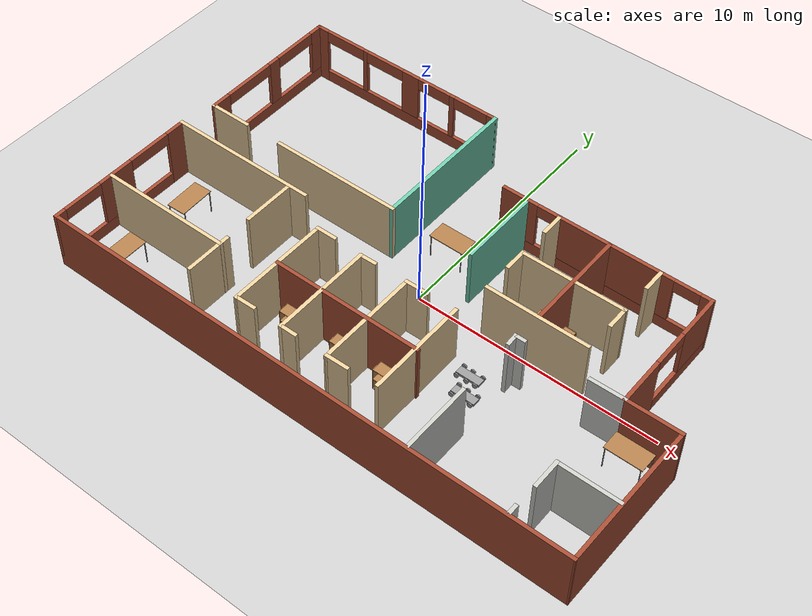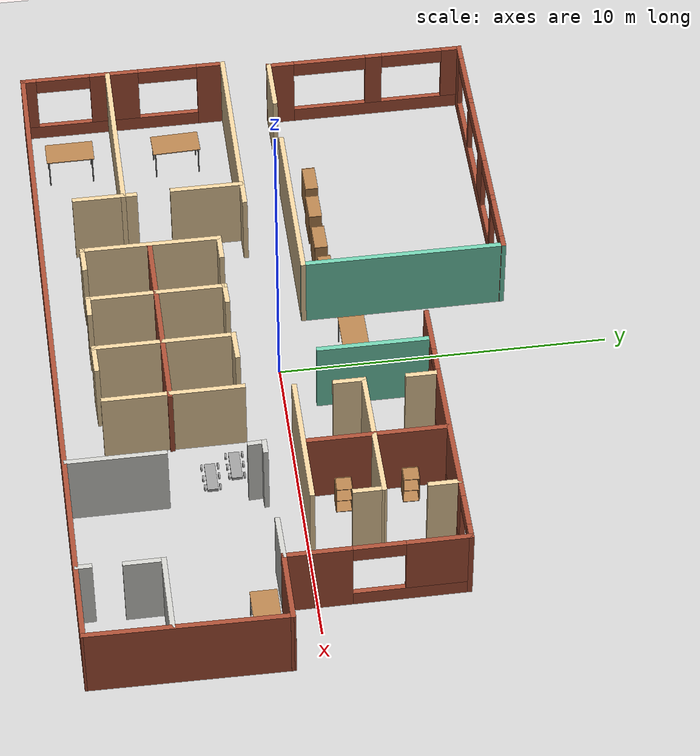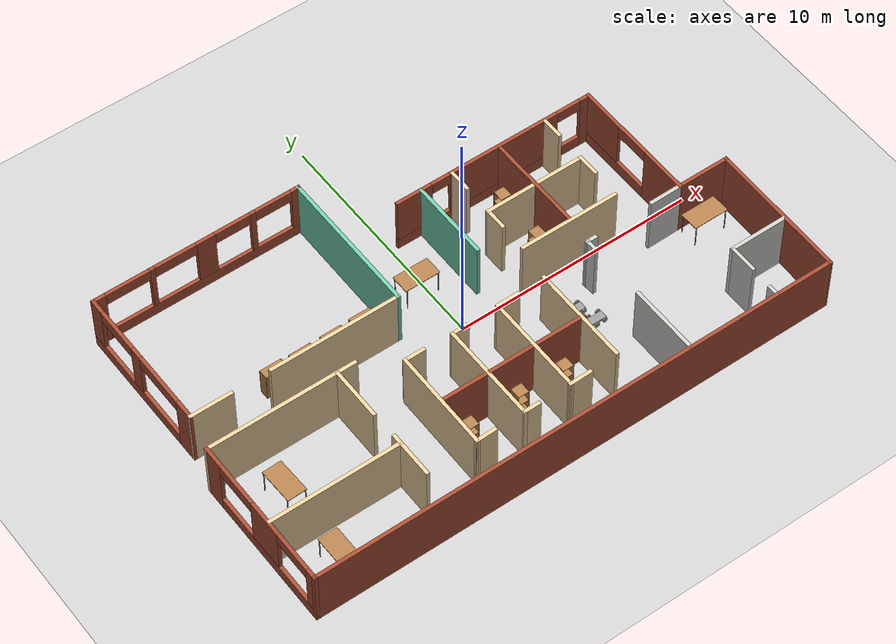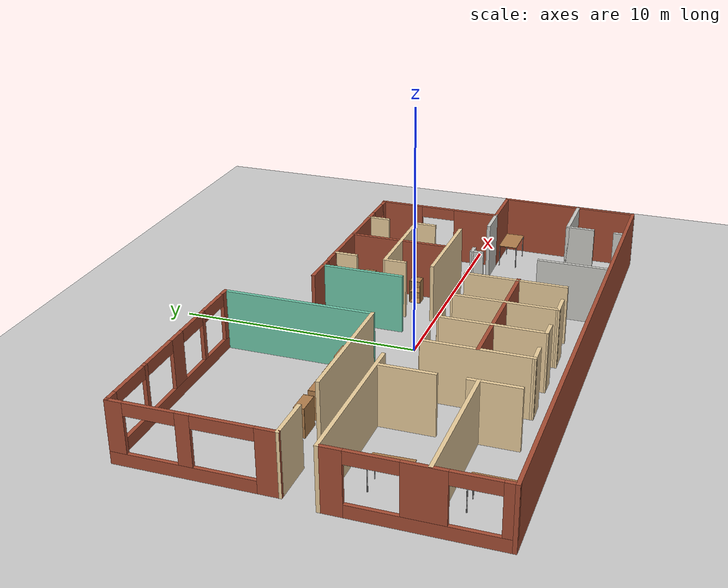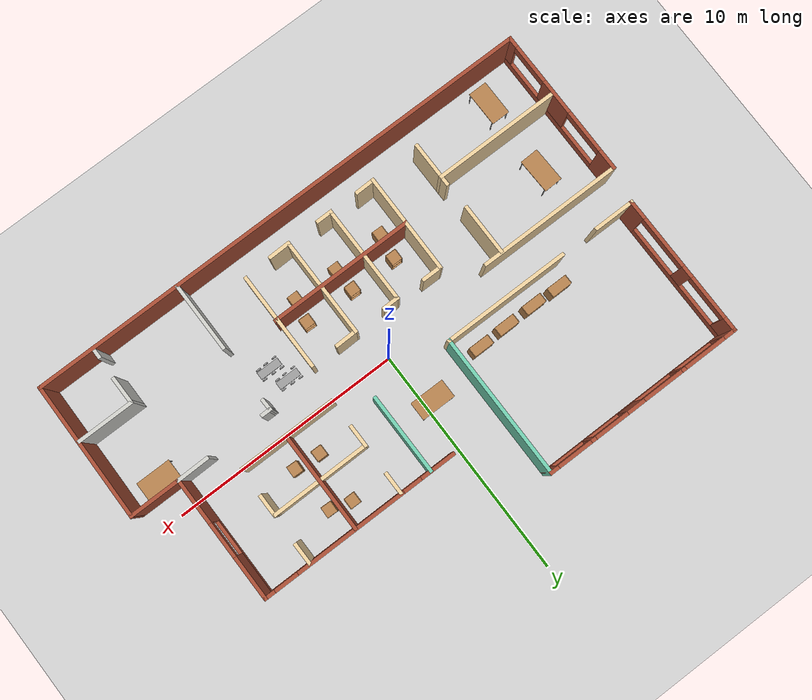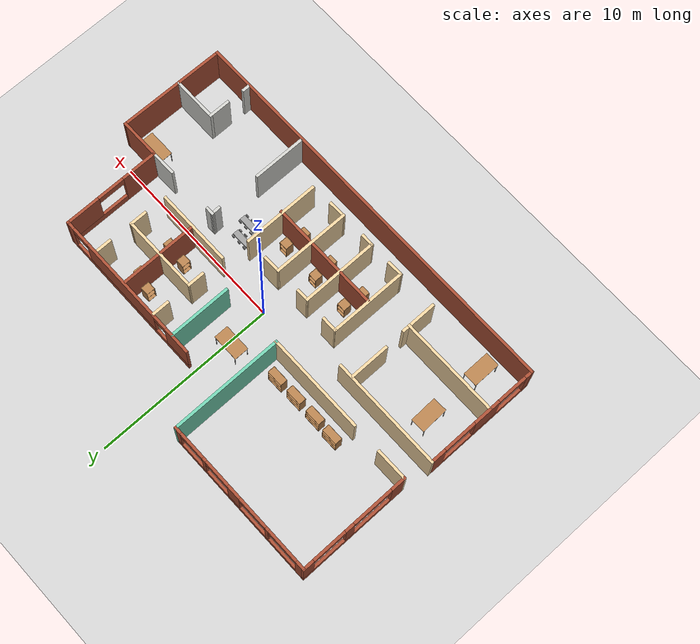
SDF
<sdf version="1.6">
 <world name="default">
  <plugin name="hello" filename="libhello.so"/>
  <light name="sun" type="directional">
   <pose>0 0 10 0 -0 0</pose>
   <diffuse>0.8 0.8 0.8 1</diffuse>
   <specular>0.2 0.2 0.2 1</specular>
   <attenuation>
    <range>1000</range>
    <constant>0.9</constant>
    <linear>0.01</linear>
    <quadratic>0.001</quadratic>
   </attenuation>
   <direction>-0.5 0.1 -0.9</direction>
  </light>
  <model name="ground_plane">
   <static>1</static>
   <link name="link">
    <collision name="collision">
     <geometry><plane><normal>0 0 1</normal><size>100 100</size></plane></geometry>
     <surface><friction><ode><mu>100</mu><mu2>50</mu2></ode></friction></surface>
    </collision>
    <visual name="visual">
     <cast_shadows>0</cast_shadows>
     <geometry><plane><normal>0 0 1</normal><size>100 100</size></plane></geometry>
     <material>
      <script><uri>file://media/materials/scripts/gazebo.material</uri><name>Gazebo/Grey</name></script>
     </material>
    </visual>
   </link>
  </model>
  <gravity>0 0 -9.8</gravity>
  <magnetic_field>6e-06 2.3e-05 -4.2e-05</magnetic_field>
  <atmosphere type="adiabatic"/>
  <physics name="default_physics" default="0" type="ode">
   <max_step_size>0.001</max_step_size>
   <real_time_factor>1</real_time_factor>
   <real_time_update_rate>1000</real_time_update_rate>
  </physics>
  <scene><ambient>0.4 0.4 0.4 1</ambient><background>0.7 0.7 0.7 1</background><shadows>1</shadows></scene>
  <spherical_coordinates>
   <surface_model>EARTH_WGS84</surface_model>
   <latitude_deg>0</latitude_deg>
   <longitude_deg>0</longitude_deg>
   <elevation>0</elevation>
   <heading_deg>0</heading_deg>
  </spherical_coordinates>
  <model name="Building_0">
   <pose>0.05167 0.163501 0 0 -0 0</pose>
   <link name="Wall_0">
    <collision name="Wall_0_Collision">
     <geometry><box><size>1.81111 0.15 2.5</size></box></geometry>
     <pose>0 0 1.25 0 -0 0</pose>
    </collision>
    <visual name="Wall_0_Visual">
     <pose>0 0 1.25 0 -0 0</pose>
     <geometry><box><size>1.81111 0.15 2.5</size></box></geometry>
     <material>
      <script><uri>file://media/materials/scripts/gazebo.material</uri><name>Gazebo/Grey</name></script>
      <ambient>0.921569 0.807843 0.615686 1</ambient>
     </material>
     <meta><layer>0</layer></meta>
    </visual>
    <pose>-9.94044 0.832232 0 0 -0 3.14159</pose>
   </link>
   <link name="Wall_1">
    <pose>-10.7784 3.88973 0 0 -0 1.57325</pose>
    <visual name="Wall_1_Visual_0">
     <pose>-2.69664 0 1.25 0 -0 0</pose>
     <geometry><box><size>0.871954 0.15 2.5</size></box></geometry>
     <material>
      <script><uri>file://media/materials/scripts/gazebo.material</uri><name>Gazebo/Bricks</name></script>
      <ambient>1 1 1 1</ambient>
     </material>
     <meta><layer>0</layer></meta>
    </visual>
    <collision name="Wall_1_Collision_0">
     <geometry><box><size>0.871954 0.15 2.5</size></box></geometry>
     <pose>-2.69664 0 1.25 0 -0 0</pose>
    </collision>
    <visual name="Wall_1_Visual_1">
     <pose>0.435977 0 0.25 0 -0 0</pose>
     <geometry><box><size>5.39327 0.15 0.5</size></box></geometry>
     <material>
      <script><uri>file://media/materials/scripts/gazebo.material</uri><name>Gazebo/Bricks</name></script>
      <ambient>1 1 1 1</ambient>
     </material>
     <meta><layer>0</layer></meta>
    </visual>
    <collision name="Wall_1_Collision_1">
     <geometry><box><size>5.39327 0.15 0.5</size></box></geometry>
     <pose>0.435977 0 0.25 0 -0 0</pose>
    </collision>
    <visual name="Wall_1_Visual_2">
     <pose>0.290907 0 1.5 0 -0 0</pose>
     <geometry><box><size>0.529134 0.15 2</size></box></geometry>
     <material>
      <script><uri>file://media/materials/scripts/gazebo.material</uri><name>Gazebo/Bricks</name></script>
      <ambient>1 1 1 1</ambient>
     </material>
     <meta><layer>0</layer></meta>
    </visual>
    <collision name="Wall_1_Collision_2">
     <geometry><box><size>0.529134 0.15 2</size></box></geometry>
     <pose>0.290907 0 1.5 0 -0 0</pose>
    </collision>
    <visual name="Wall_1_Visual_3">
     <pose>2.80354 0 1.5 0 -0 0</pose>
     <geometry><box><size>0.658139 0.15 2</size></box></geometry>
     <material>
      <script><uri>file://media/materials/scripts/gazebo.material</uri><name>Gazebo/Bricks</name></script>
      <ambient>1 1 1 1</ambient>
     </material>
     <meta><layer>0</layer></meta>
    </visual>
    <collision name="Wall_1_Collision_3">
     <geometry><box><size>0.658139 0.15 2</size></box></geometry>
     <pose>2.80354 0 1.5 0 -0 0</pose>
    </collision>
    <visual name="Wall_1_Visual_4">
     <pose>-1.11716 0 2.25 0 -0 0</pose>
     <geometry><box><size>2.287 0.15 0.5</size></box></geometry>
     <material>
      <script><uri>file://media/materials/scripts/gazebo.material</uri><name>Gazebo/Bricks</name></script>
      <ambient>1 1 1 1</ambient>
     </material>
     <meta><layer>0</layer></meta>
    </visual>
    <collision name="Wall_1_Collision_4">
     <geometry><box><size>2.287 0.15 0.5</size></box></geometry>
     <pose>-1.11716 0 2.25 0 -0 0</pose>
    </collision>
    <visual name="Wall_1_Visual_5">
     <pose>1.51497 0 2.25 0 -0 0</pose>
     <geometry><box><size>1.919 0.15 0.5</size></box></geometry>
     <material>
      <script><uri>file://media/materials/scripts/gazebo.material</uri><name>Gazebo/Bricks</name></script>
      <ambient>1 1 1 1</ambient>
     </material>
     <meta><layer>0</layer></meta>
    </visual>
    <collision name="Wall_1_Collision_5">
     <geometry><box><size>1.919 0.15 0.5</size></box></geometry>
     <pose>1.51497 0 2.25 0 -0 0</pose>
    </collision>
   </link>
   <link name="Wall_10">
    <collision name="Wall_10_Collision">
     <geometry><box><size>2.28143 0.15 2.5</size></box></geometry>
     <pose>0 0 1.25 0 -0 0</pose>
    </collision>
    <visual name="Wall_10_Visual">
     <pose>0 0 1.25 0 -0 0</pose>
     <geometry><box><size>2.28143 0.15 2.5</size></box></geometry>
     <material>
      <script><uri>file://media/materials/scripts/gazebo.material</uri><name>Gazebo/Bricks</name></script>
      <ambient>1 1 1 1</ambient>
     </material>
     <meta><layer>0</layer></meta>
    </visual>
    <pose>9.99956 -1.11177 0 0 -0 3.14159</pose>
   </link>
   <link name="Wall_11">
    <pose>8.93406 1.56323 0 0 -0 1.5708</pose>
    <visual name="Wall_11_Visual_0">
     <pose>-1.73209 0 1.25 0 -0 0</pose>
     <geometry><box><size>2.03581 0.15 2.5</size></box></geometry>
     <material>
      <script><uri>file://media/materials/scripts/gazebo.material</uri><name>Gazebo/Bricks</name></script>
      <ambient>1 1 1 1</ambient>
     </material>
     <meta><layer>0</layer></meta>
    </visual>
    <collision name="Wall_11_Collision_0">
     <geometry><box><size>2.03581 0.15 2.5</size></box></geometry>
     <pose>-1.73209 0 1.25 0 -0 0</pose>
    </collision>
    <visual name="Wall_11_Visual_1">
     <pose>1.01791 0 0.25 0 -0 0</pose>
     <geometry><box><size>3.46419 0.15 0.5</size></box></geometry>
     <material>
      <script><uri>file://media/materials/scripts/gazebo.material</uri><name>Gazebo/Bricks</name></script>
      <ambient>1 1 1 1</ambient>
     </material>
     <meta><layer>0</layer></meta>
    </visual>
    <collision name="Wall_11_Collision_1">
     <geometry><box><size>3.46419 0.15 0.5</size></box></geometry>
     <pose>1.01791 0 0.25 0 -0 0</pose>
    </collision>
    <visual name="Wall_11_Visual_2">
     <pose>1.7809 0 1.5 0 -0 0</pose>
     <geometry><box><size>1.93819 0.15 2</size></box></geometry>
     <material>
      <script><uri>file://media/materials/scripts/gazebo.material</uri><name>Gazebo/Bricks</name></script>
      <ambient>1 1 1 1</ambient>
     </material>
     <meta><layer>0</layer></meta>
    </visual>
    <collision name="Wall_11_Collision_2">
     <geometry><box><size>1.93819 0.15 2</size></box></geometry>
     <pose>1.7809 0 1.5 0 -0 0</pose>
    </collision>
    <visual name="Wall_11_Visual_3">
     <pose>0.04881 0 2.25 0 -0 0</pose>
     <geometry><box><size>1.526 0.15 0.5</size></box></geometry>
     <material>
      <script><uri>file://media/materials/scripts/gazebo.material</uri><name>Gazebo/Bricks</name></script>
      <ambient>1 1 1 1</ambient>
     </material>
     <meta><layer>0</layer></meta>
    </visual>
    <collision name="Wall_11_Collision_3">
     <geometry><box><size>1.526 0.15 0.5</size></box></geometry>
     <pose>0.04881 0 2.25 0 -0 0</pose>
    </collision>
   </link>
   <link name="Wall_12">
    <pose>4.63406 4.23823 0 0 -0 3.14159</pose>
    <visual name="Wall_12_Visual_0">
     <pose>-4.12362 0 1.25 0 -0 0</pose>
     <geometry><box><size>0.502759 0.15 2.5</size></box></geometry>
     <material>
      <script><uri>file://media/materials/scripts/gazebo.material</uri><name>Gazebo/Bricks</name></script>
      <ambient>1 1 1 1</ambient>
     </material>
     <meta><layer>0</layer></meta>
    </visual>
    <collision name="Wall_12_Collision_0">
     <geometry><box><size>0.502759 0.15 2.5</size></box></geometry>
     <pose>-4.12362 0 1.25 0 -0 0</pose>
    </collision>
    <visual name="Wall_12_Visual_1">
     <pose>0.25138 0 0.25 0 -0 0</pose>
     <geometry><box><size>8.24724 0.15 0.5</size></box></geometry>
     <material>
      <script><uri>file://media/materials/scripts/gazebo.material</uri><name>Gazebo/Bricks</name></script>
      <ambient>1 1 1 1</ambient>
     </material>
     <meta><layer>0</layer></meta>
    </visual>
    <collision name="Wall_12_Collision_1">
     <geometry><box><size>8.24724 0.15 0.5</size></box></geometry>
     <pose>0.25138 0 0.25 0 -0 0</pose>
    </collision>
    <visual name="Wall_12_Visual_2">
     <pose>-0.402272 0 1.5 0 -0 0</pose>
     <geometry><box><size>4.85594 0.15 2</size></box></geometry>
     <material>
      <script><uri>file://media/materials/scripts/gazebo.material</uri><name>Gazebo/Bricks</name></script>
      <ambient>1 1 1 1</ambient>
     </material>
     <meta><layer>0</layer></meta>
    </visual>
    <collision name="Wall_12_Collision_2">
     <geometry><box><size>4.85594 0.15 2</size></box></geometry>
     <pose>-0.402272 0 1.5 0 -0 0</pose>
    </collision>
    <visual name="Wall_12_Visual_3">
     <pose>3.60035 0 1.5 0 -0 0</pose>
     <geometry><box><size>1.5493 0.15 2</size></box></geometry>
     <material>
      <script><uri>file://media/materials/scripts/gazebo.material</uri><name>Gazebo/Bricks</name></script>
      <ambient>1 1 1 1</ambient>
     </material>
     <meta><layer>0</layer></meta>
    </visual>
    <collision name="Wall_12_Collision_3">
     <geometry><box><size>1.5493 0.15 2</size></box></geometry>
     <pose>3.60035 0 1.5 0 -0 0</pose>
    </collision>
    <visual name="Wall_12_Visual_4">
     <pose>-3.35124 0 2.25 0 -0 0</pose>
     <geometry><box><size>1.042 0.15 0.5</size></box></geometry>
     <material>
      <script><uri>file://media/materials/scripts/gazebo.material</uri><name>Gazebo/Bricks</name></script>
      <ambient>1 1 1 1</ambient>
     </material>
     <meta><layer>0</layer></meta>
    </visual>
    <collision name="Wall_12_Collision_4">
     <geometry><box><size>1.042 0.15 0.5</size></box></geometry>
     <pose>-3.35124 0 2.25 0 -0 0</pose>
    </collision>
    <visual name="Wall_12_Visual_5">
     <pose>2.4257 0 2.25 0 -0 0</pose>
     <geometry><box><size>0.8 0.15 0.5</size></box></geometry>
     <material>
      <script><uri>file://media/materials/scripts/gazebo.material</uri><name>Gazebo/Bricks</name></script>
      <ambient>1 1 1 1</ambient>
     </material>
     <meta><layer>0</layer></meta>
    </visual>
    <collision name="Wall_12_Collision_5">
     <geometry><box><size>0.8 0.15 0.5</size></box></geometry>
     <pose>2.4257 0 2.25 0 -0 0</pose>
    </collision>
   </link>
   <link name="Wall_14">
    <collision name="Wall_14_Collision">
     <geometry><box><size>5.5 0.15 2.5</size></box></geometry>
     <pose>0 0 1.25 0 -0 0</pose>
    </collision>
    <visual name="Wall_14_Visual">
     <pose>0 0 1.25 0 -0 0</pose>
     <geometry><box><size>5.5 0.15 2.5</size></box></geometry>
     <material>
      <script><uri>file://media/materials/scripts/gazebo.material</uri><name>Gazebo/Grey</name></script>
      <ambient>0.921569 0.807843 0.615686 1</ambient>
     </material>
     <meta><layer>0</layer></meta>
    </visual>
    <pose>-8.34794 -4.28377 0 0 -0 0</pose>
   </link>
   <link name="Wall_16">
    <collision name="Wall_16_Collision">
     <geometry><box><size>2.25 0.15 2.5</size></box></geometry>
     <pose>0 0 1.25 0 -0 0</pose>
    </collision>
    <visual name="Wall_16_Visual">
     <pose>0 0 1.25 0 -0 0</pose>
     <geometry><box><size>2.25 0.15 2.5</size></box></geometry>
     <material>
      <script><uri>file://media/materials/scripts/gazebo.material</uri><name>Gazebo/Grey</name></script>
      <ambient>0.921569 0.807843 0.615686 1</ambient>
     </material>
     <meta><layer>0</layer></meta>
    </visual>
    <pose>-5.71094 -1.71077 0 0 0 -1.5708</pose>
   </link>
   <link name="Wall_18">
    <collision name="Wall_18_Collision">
     <geometry><box><size>2 0.15 2.5</size></box></geometry>
     <pose>0 0 1.25 0 -0 0</pose>
    </collision>
    <visual name="Wall_18_Visual">
     <pose>0 0 1.25 0 -0 0</pose>
     <geometry><box><size>2 0.15 2.5</size></box></geometry>
     <material>
      <script><uri>file://media/materials/scripts/gazebo.material</uri><name>Gazebo/Grey</name></script>
      <ambient>0.921569 0.807843 0.615686 1</ambient>
     </material>
     <meta><layer>0</layer></meta>
    </visual>
    <pose>-5.67594 -4.85677 0 0 0 -1.5708</pose>
   </link>
   <link name="Wall_2">
    <pose>-6.44794 6.95473 0 0 -0 0.001729</pose>
    <visual name="Wall_2_Visual_0">
     <pose>-4.12925 0 1.25 0 -0 0</pose>
     <geometry><box><size>0.567323 0.15 2.5</size></box></geometry>
     <material>
      <script><uri>file://media/materials/scripts/gazebo.material</uri><name>Gazebo/Bricks</name></script>
      <ambient>1 1 1 1</ambient>
     </material>
     <meta><layer>0</layer></meta>
    </visual>
    <collision name="Wall_2_Collision_0">
     <geometry><box><size>0.567323 0.15 2.5</size></box></geometry>
     <pose>-4.12925 0 1.25 0 -0 0</pose>
    </collision>
    <visual name="Wall_2_Visual_1">
     <pose>0.283662 0 0.25 0 -0 0</pose>
     <geometry><box><size>8.2585 0.15 0.5</size></box></geometry>
     <material>
      <script><uri>file://media/materials/scripts/gazebo.material</uri><name>Gazebo/Bricks</name></script>
      <ambient>1 1 1 1</ambient>
     </material>
     <meta><layer>0</layer></meta>
    </visual>
    <collision name="Wall_2_Collision_1">
     <geometry><box><size>8.2585 0.15 0.5</size></box></geometry>
     <pose>0.283662 0 0.25 0 -0 0</pose>
    </collision>
    <visual name="Wall_2_Visual_2">
     <pose>-1.91466 0 1.5 0 -0 0</pose>
     <geometry><box><size>0.197862 0.15 2</size></box></geometry>
     <material>
      <script><uri>file://media/materials/scripts/gazebo.material</uri><name>Gazebo/Bricks</name></script>
      <ambient>1 1 1 1</ambient>
     </material>
     <meta><layer>0</layer></meta>
    </visual>
    <collision name="Wall_2_Collision_2">
     <geometry><box><size>0.197862 0.15 2</size></box></geometry>
     <pose>-1.91466 0 1.5 0 -0 0</pose>
    </collision>
    <visual name="Wall_2_Visual_3">
     <pose>0.342292 0 1.5 0 -0 0</pose>
     <geometry><box><size>0.792034 0.15 2</size></box></geometry>
     <material>
      <script><uri>file://media/materials/scripts/gazebo.material</uri><name>Gazebo/Bricks</name></script>
      <ambient>1 1 1 1</ambient>
     </material>
     <meta><layer>0</layer></meta>
    </visual>
    <collision name="Wall_2_Collision_3">
     <geometry><box><size>0.792034 0.15 2</size></box></geometry>
     <pose>0.342292 0 1.5 0 -0 0</pose>
    </collision>
    <visual name="Wall_2_Visual_4">
     <pose>2.35004 0 1.5 0 -0 0</pose>
     <geometry><box><size>0.221614 0.15 2</size></box></geometry>
     <material>
      <script><uri>file://media/materials/scripts/gazebo.material</uri><name>Gazebo/Bricks</name></script>
      <ambient>1 1 1 1</ambient>
     </material>
     <meta><layer>0</layer></meta>
    </visual>
    <collision name="Wall_2_Collision_4">
     <geometry><box><size>0.221614 0.15 2</size></box></geometry>
     <pose>2.35004 0 1.5 0 -0 0</pose>
    </collision>
    <visual name="Wall_2_Visual_5">
     <pose>4.20038 0 1.5 0 -0 0</pose>
     <geometry><box><size>0.425064 0.15 2</size></box></geometry>
     <material>
      <script><uri>file://media/materials/scripts/gazebo.material</uri><name>Gazebo/Bricks</name></script>
      <ambient>1 1 1 1</ambient>
     </material>
     <meta><layer>0</layer></meta>
    </visual>
    <collision name="Wall_2_Collision_5">
     <geometry><box><size>0.425064 0.15 2</size></box></geometry>
     <pose>4.20038 0 1.5 0 -0 0</pose>
    </collision>
    <visual name="Wall_2_Visual_6">
     <pose>-2.92959 0 2.25 0 -0 0</pose>
     <geometry><box><size>1.832 0.15 0.5</size></box></geometry>
     <material>
      <script><uri>file://media/materials/scripts/gazebo.material</uri><name>Gazebo/Bricks</name></script>
      <ambient>1 1 1 1</ambient>
     </material>
     <meta><layer>0</layer></meta>
    </visual>
    <collision name="Wall_2_Collision_6">
     <geometry><box><size>1.832 0.15 0.5</size></box></geometry>
     <pose>-2.92959 0 2.25 0 -0 0</pose>
    </collision>
    <visual name="Wall_2_Visual_7">
     <pose>-0.934725 0 2.25 0 -0 0</pose>
     <geometry><box><size>1.762 0.15 0.5</size></box></geometry>
     <material>
      <script><uri>file://media/materials/scripts/gazebo.material</uri><name>Gazebo/Bricks</name></script>
      <ambient>1 1 1 1</ambient>
     </material>
     <meta><layer>0</layer></meta>
    </visual>
    <collision name="Wall_2_Collision_7">
     <geometry><box><size>1.762 0.15 0.5</size></box></geometry>
     <pose>-0.934725 0 2.25 0 -0 0</pose>
    </collision>
    <visual name="Wall_2_Visual_8">
     <pose>1.48877 0 2.25 0 -0 0</pose>
     <geometry><box><size>1.50092 0.15 0.5</size></box></geometry>
     <material>
      <script><uri>file://media/materials/scripts/gazebo.material</uri><name>Gazebo/Bricks</name></script>
      <ambient>1 1 1 1</ambient>
     </material>
     <meta><layer>0</layer></meta>
    </visual>
    <collision name="Wall_2_Collision_8">
     <geometry><box><size>1.50092 0.15 0.5</size></box></geometry>
     <pose>1.48877 0 2.25 0 -0 0</pose>
    </collision>
    <visual name="Wall_2_Visual_9">
     <pose>3.22435 0 2.25 0 -0 0</pose>
     <geometry><box><size>1.527 0.15 0.5</size></box></geometry>
     <material>
      <script><uri>file://media/materials/scripts/gazebo.material</uri><name>Gazebo/Bricks</name></script>
      <ambient>1 1 1 1</ambient>
     </material>
     <meta><layer>0</layer></meta>
    </visual>
    <collision name="Wall_2_Collision_9">
     <geometry><box><size>1.527 0.15 0.5</size></box></geometry>
     <pose>3.22435 0 2.25 0 -0 0</pose>
    </collision>
   </link>
   <link name="Wall_20">
    <collision name="Wall_20_Collision">
     <geometry><box><size>0.91255 0.15 2.5</size></box></geometry>
     <pose>0 0 1.25 0 -0 0</pose>
    </collision>
    <visual name="Wall_20_Visual">
     <pose>0 0 1.25 0 -0 0</pose>
     <geometry><box><size>0.91255 0.15 2.5</size></box></geometry>
     <material>
      <script><uri>file://media/materials/scripts/gazebo.material</uri><name>Gazebo/Grey</name></script>
      <ambient>0.921569 0.807843 0.615686 1</ambient>
     </material>
     <meta><layer>0</layer></meta>
    </visual>
    <pose>-3.14644 -1.56577 0 0 -0 3.14159</pose>
   </link>
   <link name="Wall_21">
    <collision name="Wall_21_Collision">
     <geometry><box><size>4.32 0.15 2.5</size></box></geometry>
     <pose>0 0 1.25 0 -0 0</pose>
    </collision>
    <visual name="Wall_21_Visual">
     <pose>0 0 1.25 0 -0 0</pose>
     <geometry><box><size>4.32 0.15 2.5</size></box></geometry>
     <material>
      <script><uri>file://media/materials/scripts/gazebo.material</uri><name>Gazebo/Grey</name></script>
      <ambient>0.921569 0.807843 0.615686 1</ambient>
     </material>
     <meta><layer>0</layer></meta>
    </visual>
    <pose>-3.53644 -3.65077 0 0 0 -1.57487</pose>
   </link>
   <link name="Wall_22">
    <collision name="Wall_22_Collision">
     <geometry><box><size>0.91255 0.15 2.5</size></box></geometry>
     <pose>0 0 1.25 0 -0 0</pose>
    </collision>
    <visual name="Wall_22_Visual">
     <pose>0 0 1.25 0 -0 0</pose>
     <geometry><box><size>0.91255 0.15 2.5</size></box></geometry>
     <material>
      <script><uri>file://media/materials/scripts/gazebo.material</uri><name>Gazebo/Grey</name></script>
      <ambient>0.921569 0.807843 0.615686 1</ambient>
     </material>
     <meta><layer>0</layer></meta>
    </visual>
    <pose>-3.16394 -5.72727 0 0 -0 0.022306</pose>
   </link>
   <link name="Wall_24">
    <collision name="Wall_24_Collision">
     <geometry><box><size>6.25 0.15 2.5</size></box></geometry>
     <pose>0 0 1.25 0 -0 0</pose>
    </collision>
    <visual name="Wall_24_Visual">
     <pose>0 0 1.25 0 -0 0</pose>
     <geometry><box><size>6.25 0.15 2.5</size></box></geometry>
     <material>
      <script><uri>file://media/materials/scripts/gazebo.material</uri><name>Gazebo/Bricks</name></script>
      <ambient>1 1 1 1</ambient>
     </material>
     <meta><layer>0</layer></meta>
    </visual>
    <pose>-0.484936 -3.68277 0 0 -0 0</pose>
   </link>
   <link name="Wall_26">
    <collision name="Wall_26_Collision">
     <geometry><box><size>0.765183 0.15 2.5</size></box></geometry>
     <pose>0 0 1.25 0 -0 0</pose>
    </collision>
    <visual name="Wall_26_Visual">
     <pose>0 0 1.25 0 -0 0</pose>
     <geometry><box><size>0.765183 0.15 2.5</size></box></geometry>
     <material>
      <script><uri>file://media/materials/scripts/gazebo.material</uri><name>Gazebo/Grey</name></script>
      <ambient>0.921569 0.807843 0.615686 1</ambient>
     </material>
     <meta><layer>0</layer></meta>
    </visual>
    <pose>-1.23644 -1.60827 0 0 0 -3.11721</pose>
   </link>
   <link name="Wall_27">
    <collision name="Wall_27_Collision">
     <geometry><box><size>4.26621 0.15 2.5</size></box></geometry>
     <pose>0 0 1.25 0 -0 0</pose>
    </collision>
    <visual name="Wall_27_Visual">
     <pose>0 0 1.25 0 -0 0</pose>
     <geometry><box><size>4.26621 0.15 2.5</size></box></geometry>
     <material>
      <script><uri>file://media/materials/scripts/gazebo.material</uri><name>Gazebo/Grey</name></script>
      <ambient>0.921569 0.807843 0.615686 1</ambient>
     </material>
     <meta><layer>0</layer></meta>
    </visual>
    <pose>-1.54244 -3.67377 0 0 0 -1.57007</pose>
   </link>
   <link name="Wall_28">
    <collision name="Wall_28_Collision">
     <geometry><box><size>0.75 0.15 2.5</size></box></geometry>
     <pose>0 0 1.25 0 -0 0</pose>
    </collision>
    <visual name="Wall_28_Visual">
     <pose>0 0 1.25 0 -0 0</pose>
     <geometry><box><size>0.75 0.15 2.5</size></box></geometry>
     <material>
      <script><uri>file://media/materials/scripts/gazebo.material</uri><name>Gazebo/Grey</name></script>
      <ambient>0.921569 0.807843 0.615686 1</ambient>
     </material>
     <meta><layer>0</layer></meta>
    </visual>
    <pose>-1.24094 -5.73177 0 0 -0 0</pose>
   </link>
   <link name="Wall_3">
    <collision name="Wall_3_Collision">
     <geometry><box><size>6.28044 0.15 2.5</size></box></geometry>
     <pose>0 0 1.25 0 -0 0</pose>
    </collision>
    <visual name="Wall_3_Visual">
     <pose>0 0 1.25 0 -0 0</pose>
     <geometry><box><size>6.28044 0.15 2.5</size></box></geometry>
     <material>
      <script><uri>file://media/materials/scripts/gazebo.material</uri><name>Gazebo/Grey</name></script>
      <ambient>0.435294 0.796078 0.67451 1</ambient>
     </material>
     <meta><layer>0</layer></meta>
    </visual>
    <pose>-2.10994 3.89723 0 0 0 -1.5708</pose>
   </link>
   <link name="Wall_30">
    <collision name="Wall_30_Collision">
     <geometry><box><size>1.01749 0.15 2.5</size></box></geometry>
     <pose>0 0 1.25 0 -0 0</pose>
    </collision>
    <visual name="Wall_30_Visual">
     <pose>0 0 1.25 0 -0 0</pose>
     <geometry><box><size>1.01749 0.15 2.5</size></box></geometry>
     <material>
      <script><uri>file://media/materials/scripts/gazebo.material</uri><name>Gazebo/Grey</name></script>
      <ambient>0.921569 0.807843 0.615686 1</ambient>
     </material>
     <meta><layer>0</layer></meta>
    </visual>
    <pose>0.876564 -1.55727 0 0 0 -3.12199</pose>
   </link>
   <link name="Wall_31">
    <collision name="Wall_31_Collision">
     <geometry><box><size>4.32039 0.15 2.5</size></box></geometry>
     <pose>0 0 1.25 0 -0 0</pose>
    </collision>
    <visual name="Wall_31_Visual">
     <pose>0 0 1.25 0 -0 0</pose>
     <geometry><box><size>4.32039 0.15 2.5</size></box></geometry>
     <material>
      <script><uri>file://media/materials/scripts/gazebo.material</uri><name>Gazebo/Grey</name></script>
      <ambient>0.921569 0.807843 0.615686 1</ambient>
     </material>
     <meta><layer>0</layer></meta>
    </visual>
    <pose>0.443064 -3.65077 0 0 0 -1.5708</pose>
   </link>
   <link name="Wall_32">
    <collision name="Wall_32_Collision">
     <geometry><box><size>1 0.15 2.5</size></box></geometry>
     <pose>0 0 1.25 0 -0 0</pose>
    </collision>
    <visual name="Wall_32_Visual">
     <pose>0 0 1.25 0 -0 0</pose>
     <geometry><box><size>1 0.15 2.5</size></box></geometry>
     <material>
      <script><uri>file://media/materials/scripts/gazebo.material</uri><name>Gazebo/Grey</name></script>
      <ambient>0.921569 0.807843 0.615686 1</ambient>
     </material>
     <meta><layer>0</layer></meta>
    </visual>
    <pose>0.868064 -5.72727 0 0 -0 0.019997</pose>
   </link>
   <link name="Wall_34">
    <collision name="Wall_34_Collision">
     <geometry><box><size>4.25 0.15 2.5</size></box></geometry>
     <pose>0 0 1.25 0 -0 0</pose>
    </collision>
    <visual name="Wall_34_Visual">
     <pose>0 0 1.25 0 -0 0</pose>
     <geometry><box><size>4.25 0.15 2.5</size></box></geometry>
     <material>
      <script><uri>file://media/materials/scripts/gazebo.material</uri><name>Gazebo/Grey</name></script>
      <ambient>0.921569 0.807843 0.615686 1</ambient>
     </material>
     <meta><layer>0</layer></meta>
    </visual>
    <pose>2.49906 -3.58077 0 0 0 -1.5708</pose>
   </link>
   <link name="Wall_36">
    <collision name="Wall_36_Collision">
     <geometry><box><size>3 0.15 2.5</size></box></geometry>
     <pose>0 0 1.25 0 -0 0</pose>
    </collision>
    <visual name="Wall_36_Visual">
     <pose>0 0 1.25 0 -0 0</pose>
     <geometry><box><size>3 0.15 2.5</size></box></geometry>
     <material>
      <script><uri>file://media/materials/scripts/gazebo.material</uri><name>Gazebo/CeilingTiled</name></script>
      <ambient>1 1 1 1</ambient>
     </material>
     <meta><layer>0</layer></meta>
    </visual>
    <pose>4.72106 -5.47477 0 0 0 -1.5708</pose>
   </link>
   <link name="Wall_38">
    <collision name="Wall_38_Collision">
     <geometry><box><size>0.570324 0.15 2.5</size></box></geometry>
     <pose>0 0 1.25 0 -0 0</pose>
    </collision>
    <visual name="Wall_38_Visual">
     <pose>0 0 1.25 0 -0 0</pose>
     <geometry><box><size>0.570324 0.15 2.5</size></box></geometry>
     <material>
      <script><uri>file://media/materials/scripts/gazebo.material</uri><name>Gazebo/CeilingTiled</name></script>
      <ambient>1 1 1 1</ambient>
     </material>
     <meta><layer>0</layer></meta>
    </visual>
    <pose>4.71206 -1.37377 0 0 -0 1.61363</pose>
   </link>
   <link name="Wall_39">
    <collision name="Wall_39_Collision">
     <geometry><box><size>0.5 0.15 2.5</size></box></geometry>
     <pose>0 0 1.25 0 -0 0</pose>
    </collision>
    <visual name="Wall_39_Visual">
     <pose>0 0 1.25 0 -0 0</pose>
     <geometry><box><size>0.5 0.15 2.5</size></box></geometry>
     <material>
      <script><uri>file://media/materials/scripts/gazebo.material</uri><name>Gazebo/CeilingTiled</name></script>
      <ambient>1 1 1 1</ambient>
     </material>
     <meta><layer>0</layer></meta>
    </visual>
    <pose>4.87806 -1.16377 0 0 -0 0</pose>
   </link>
   <link name="Wall_4">
    <collision name="Wall_4_Collision">
     <geometry><box><size>5.5 0.15 2.5</size></box></geometry>
     <pose>0 0 1.25 0 -0 0</pose>
    </collision>
    <visual name="Wall_4_Visual">
     <pose>0 0 1.25 0 -0 0</pose>
     <geometry><box><size>5.5 0.15 2.5</size></box></geometry>
     <material>
      <script><uri>file://media/materials/scripts/gazebo.material</uri><name>Gazebo/Grey</name></script>
      <ambient>0.921569 0.807843 0.615686 1</ambient>
     </material>
     <meta><layer>0</layer></meta>
    </visual>
    <pose>-4.78494 0.832232 0 0 -0 3.14159</pose>
   </link>
   <link name="Wall_41">
    <collision name="Wall_41_Collision">
     <geometry><box><size>1.46 0.15 2.5</size></box></geometry>
     <pose>0 0 1.25 0 -0 0</pose>
    </collision>
    <visual name="Wall_41_Visual">
     <pose>0 0 1.25 0 -0 0</pose>
     <geometry><box><size>1.46 0.15 2.5</size></box></geometry>
     <material>
      <script><uri>file://media/materials/scripts/gazebo.material</uri><name>Gazebo/CeilingTiled</name></script>
      <ambient>1 1 1 1</ambient>
     </material>
     <meta><layer>0</layer></meta>
    </visual>
    <pose>8.27906 -1.12027 0 0 -0 0.012976</pose>
   </link>
   <link name="Wall_43">
    <collision name="Wall_43_Collision">
     <geometry><box><size>2.5 0.15 2.5</size></box></geometry>
     <pose>0 0 1.25 0 -0 0</pose>
    </collision>
    <visual name="Wall_43_Visual">
     <pose>0 0 1.25 0 -0 0</pose>
     <geometry><box><size>2.5 0.15 2.5</size></box></geometry>
     <material>
      <script><uri>file://media/materials/scripts/gazebo.material</uri><name>Gazebo/CeilingTiled</name></script>
      <ambient>1 1 1 1</ambient>
     </material>
     <meta><layer>0</layer></meta>
    </visual>
    <pose>9.80706 -4.46977 0 0 -0 3.14159</pose>
   </link>
   <link name="Wall_44">
    <collision name="Wall_44_Collision">
     <geometry><box><size>1.25 0.15 2.5</size></box></geometry>
     <pose>0 0 1.25 0 -0 0</pose>
    </collision>
    <visual name="Wall_44_Visual">
     <pose>0 0 1.25 0 -0 0</pose>
     <geometry><box><size>1.25 0.15 2.5</size></box></geometry>
     <material>
      <script><uri>file://media/materials/scripts/gazebo.material</uri><name>Gazebo/CeilingTiled</name></script>
      <ambient>1 1 1 1</ambient>
     </material>
     <meta><layer>0</layer></meta>
    </visual>
    <pose>8.63206 -5.01977 0 0 0 -1.5708</pose>
   </link>
   <link name="Wall_46">
    <collision name="Wall_46_Collision">
     <geometry><box><size>0.5 0.15 2.5</size></box></geometry>
     <pose>0 0 1.25 0 -0 0</pose>
    </collision>
    <visual name="Wall_46_Visual">
     <pose>0 0 1.25 0 -0 0</pose>
     <geometry><box><size>0.5 0.15 2.5</size></box></geometry>
     <material>
      <script><uri>file://media/materials/scripts/gazebo.material</uri><name>Gazebo/CeilingTiled</name></script>
      <ambient>1 1 1 1</ambient>
     </material>
     <meta><layer>0</layer></meta>
    </visual>
    <pose>8.58606 -6.74377 0 0 0 -1.5708</pose>
   </link>
   <link name="Wall_48">
    <collision name="Wall_48_Collision">
     <geometry><box><size>3.5 0.15 2.5</size></box></geometry>
     <pose>0 0 1.25 0 -0 0</pose>
    </collision>
    <visual name="Wall_48_Visual">
     <pose>0 0 1.25 0 -0 0</pose>
     <geometry><box><size>3.5 0.15 2.5</size></box></geometry>
     <material>
      <script><uri>file://media/materials/scripts/gazebo.material</uri><name>Gazebo/Grey</name></script>
      <ambient>0.435294 0.796078 0.67451 1</ambient>
     </material>
     <meta><layer>0</layer></meta>
    </visual>
    <pose>1.36306 2.54023 0 0 0 -1.5708</pose>
   </link>
   <link name="Wall_50">
    <collision name="Wall_50_Collision">
     <geometry><box><size>1 0.15 2.5</size></box></geometry>
     <pose>0 0 1.25 0 -0 0</pose>
    </collision>
    <visual name="Wall_50_Visual">
     <pose>0 0 1.25 0 -0 0</pose>
     <geometry><box><size>1 0.15 2.5</size></box></geometry>
     <material>
      <script><uri>file://media/materials/scripts/gazebo.material</uri><name>Gazebo/Grey</name></script>
      <ambient>0.921569 0.807843 0.615686 1</ambient>
     </material>
     <meta><layer>0</layer></meta>
    </visual>
    <pose>2.72706 3.75523 0 0 0 -1.5708</pose>
   </link>
   <link name="Wall_52">
    <collision name="Wall_52_Collision">
     <geometry><box><size>1 0.15 2.5</size></box></geometry>
     <pose>0 0 1.25 0 -0 0</pose>
    </collision>
    <visual name="Wall_52_Visual">
     <pose>0 0 1.25 0 -0 0</pose>
     <geometry><box><size>1 0.15 2.5</size></box></geometry>
     <material>
      <script><uri>file://media/materials/scripts/gazebo.material</uri><name>Gazebo/Grey</name></script>
      <ambient>0.921569 0.807843 0.615686 1</ambient>
     </material>
     <meta><layer>0</layer></meta>
    </visual>
    <pose>6.90706 3.79023 0 0 0 -1.5708</pose>
   </link>
   <link name="Wall_54">
    <collision name="Wall_54_Collision">
     <geometry><box><size>4.25 0.15 2.5</size></box></geometry>
     <pose>0 0 1.25 0 -0 0</pose>
    </collision>
    <visual name="Wall_54_Visual">
     <pose>0 0 1.25 0 -0 0</pose>
     <geometry><box><size>4.25 0.15 2.5</size></box></geometry>
     <material>
      <script><uri>file://media/materials/scripts/gazebo.material</uri><name>Gazebo/Bricks</name></script>
      <ambient>1 1 1 1</ambient>
     </material>
     <meta><layer>0</layer></meta>
    </visual>
    <pose>4.82606 2.14823 0 0 0 -1.5708</pose>
   </link>
   <link name="Wall_56">
    <collision name="Wall_56_Collision">
     <geometry><box><size>4.25 0.15 2.5</size></box></geometry>
     <pose>0 0 1.25 0 -0 0</pose>
    </collision>
    <visual name="Wall_56_Visual">
     <pose>0 0 1.25 0 -0 0</pose>
     <geometry><box><size>4.25 0.15 2.5</size></box></geometry>
     <material>
      <script><uri>file://media/materials/scripts/gazebo.material</uri><name>Gazebo/Grey</name></script>
      <ambient>0.921569 0.807843 0.615686 1</ambient>
     </material>
     <meta><layer>0</layer></meta>
    </visual>
    <pose>4.75906 -0.034768 0 0 -0 0</pose>
   </link>
   <link name="Wall_59">
    <collision name="Wall_59_Collision">
     <geometry><box><size>4.32 0.15 2.5</size></box></geometry>
     <pose>0 0 1.25 0 -0 0</pose>
    </collision>
    <visual name="Wall_59_Visual">
     <pose>0 0 1.25 0 -0 0</pose>
     <geometry><box><size>4.32 0.15 2.5</size></box></geometry>
     <material>
      <script><uri>file://media/materials/scripts/gazebo.material</uri><name>Gazebo/Grey</name></script>
      <ambient>0.921569 0.807843 0.615686 1</ambient>
     </material>
     <meta><layer>0</layer></meta>
    </visual>
    <pose>4.79406 2.03123 0 0 -0 0.004317</pose>
   </link>
   <link name="Wall_6">
    <collision name="Wall_6_Collision">
     <geometry><box><size>6.25 0.15 2.5</size></box></geometry>
     <pose>0 0 1.25 0 -0 0</pose>
    </collision>
    <visual name="Wall_6_Visual">
     <pose>0 0 1.25 0 -0 0</pose>
     <geometry><box><size>6.25 0.15 2.5</size></box></geometry>
     <material>
      <script><uri>file://media/materials/scripts/gazebo.material</uri><name>Gazebo/Grey</name></script>
      <ambient>0.921569 0.807843 0.615686 1</ambient>
     </material>
     <meta><layer>0</layer></meta>
    </visual>
    <pose>-8.01594 -0.611768 0 0 -0 3.14159</pose>
   </link>
   <link name="Wall_60">
    <collision name="Wall_60_Collision">
     <geometry><box><size>1 0.15 2.5</size></box></geometry>
     <pose>0 0 1.25 0 -0 0</pose>
    </collision>
    <visual name="Wall_60_Visual">
     <pose>0 0 1.25 0 -0 0</pose>
     <geometry><box><size>1 0.15 2.5</size></box></geometry>
     <material>
      <script><uri>file://media/materials/scripts/gazebo.material</uri><name>Gazebo/Grey</name></script>
      <ambient>0.921569 0.807843 0.615686 1</ambient>
     </material>
     <meta><layer>0</layer></meta>
    </visual>
    <pose>6.87906 1.61523 0 0 0 -1.5708</pose>
   </link>
   <link name="Wall_62">
    <collision name="Wall_62_Collision">
     <geometry><box><size>1 0.15 2.5</size></box></geometry>
     <pose>0 0 1.25 0 -0 0</pose>
    </collision>
    <visual name="Wall_62_Visual">
     <pose>0 0 1.25 0 -0 0</pose>
     <geometry><box><size>1 0.15 2.5</size></box></geometry>
     <material>
      <script><uri>file://media/materials/scripts/gazebo.material</uri><name>Gazebo/Grey</name></script>
      <ambient>0.921569 0.807843 0.615686 1</ambient>
     </material>
     <meta><layer>0</layer></meta>
    </visual>
    <pose>2.70906 1.59723 0 0 0 -1.5708</pose>
   </link>
   <link name="Wall_7">
    <pose>-11.0659 -3.78677 0 0 0 -1.5708</pose>
    <visual name="Wall_7_Visual_0">
     <pose>-2.79306 0 1.25 0 -0 0</pose>
     <geometry><box><size>0.913886 0.15 2.5</size></box></geometry>
     <material>
      <script><uri>file://media/materials/scripts/gazebo.material</uri><name>Gazebo/Bricks</name></script>
      <ambient>1 1 1 1</ambient>
     </material>
     <meta><layer>0</layer></meta>
    </visual>
    <collision name="Wall_7_Collision_0">
     <geometry><box><size>0.913886 0.15 2.5</size></box></geometry>
     <pose>-2.79306 0 1.25 0 -0 0</pose>
    </collision>
    <visual name="Wall_7_Visual_1">
     <pose>0.456943 0 0.25 0 -0 0</pose>
     <geometry><box><size>5.58611 0.15 0.5</size></box></geometry>
     <material>
      <script><uri>file://media/materials/scripts/gazebo.material</uri><name>Gazebo/Bricks</name></script>
      <ambient>1 1 1 1</ambient>
     </material>
     <meta><layer>0</layer></meta>
    </visual>
    <collision name="Wall_7_Collision_1">
     <geometry><box><size>5.58611 0.15 0.5</size></box></geometry>
     <pose>0.456943 0 0.25 0 -0 0</pose>
    </collision>
    <visual name="Wall_7_Visual_2">
     <pose>0.299371 0 1.5 0 -0 0</pose>
     <geometry><box><size>1.54097 0.15 2</size></box></geometry>
     <material>
      <script><uri>file://media/materials/scripts/gazebo.material</uri><name>Gazebo/Bricks</name></script>
      <ambient>1 1 1 1</ambient>
     </material>
     <meta><layer>0</layer></meta>
    </visual>
    <collision name="Wall_7_Collision_2">
     <geometry><box><size>1.54097 0.15 2</size></box></geometry>
     <pose>0.299371 0 1.5 0 -0 0</pose>
    </collision>
    <visual name="Wall_7_Visual_3">
     <pose>3.00593 0 1.5 0 -0 0</pose>
     <geometry><box><size>0.488144 0.15 2</size></box></geometry>
     <material>
      <script><uri>file://media/materials/scripts/gazebo.material</uri><name>Gazebo/Bricks</name></script>
      <ambient>1 1 1 1</ambient>
     </material>
     <meta><layer>0</layer></meta>
    </visual>
    <collision name="Wall_7_Collision_3">
     <geometry><box><size>0.488144 0.15 2</size></box></geometry>
     <pose>3.00593 0 1.5 0 -0 0</pose>
    </collision>
    <visual name="Wall_7_Visual_4">
     <pose>-1.40361 0 2.25 0 -0 0</pose>
     <geometry><box><size>1.865 0.15 0.5</size></box></geometry>
     <material>
      <script><uri>file://media/materials/scripts/gazebo.material</uri><name>Gazebo/Bricks</name></script>
      <ambient>1 1 1 1</ambient>
     </material>
     <meta><layer>0</layer></meta>
    </visual>
    <collision name="Wall_7_Collision_4">
     <geometry><box><size>1.865 0.15 0.5</size></box></geometry>
     <pose>-1.40361 0 2.25 0 -0 0</pose>
    </collision>
    <visual name="Wall_7_Visual_5">
     <pose>1.91586 0 2.25 0 -0 0</pose>
     <geometry><box><size>1.692 0.15 0.5</size></box></geometry>
     <material>
      <script><uri>file://media/materials/scripts/gazebo.material</uri><name>Gazebo/Bricks</name></script>
      <ambient>1 1 1 1</ambient>
     </material>
     <meta><layer>0</layer></meta>
    </visual>
    <collision name="Wall_7_Collision_5">
     <geometry><box><size>1.692 0.15 0.5</size></box></geometry>
     <pose>1.91586 0 2.25 0 -0 0</pose>
    </collision>
   </link>
   <link name="Wall_8">
    <collision name="Wall_8_Collision">
     <geometry><box><size>22.211 0.15 2.5</size></box></geometry>
     <pose>0 0 1.25 0 -0 0</pose>
    </collision>
    <visual name="Wall_8_Visual">
     <pose>0 0 1.25 0 -0 0</pose>
     <geometry><box><size>22.211 0.15 2.5</size></box></geometry>
     <material>
      <script><uri>file://media/materials/scripts/gazebo.material</uri><name>Gazebo/Bricks</name></script>
      <ambient>1 1 1 1</ambient>
     </material>
     <meta><layer>0</layer></meta>
    </visual>
    <pose>-0.035436 -6.96177 0 0 -0 0</pose>
   </link>
   <link name="Wall_9">
    <collision name="Wall_9_Collision">
     <geometry><box><size>6 0.15 2.5</size></box></geometry>
     <pose>0 0 1.25 0 -0 0</pose>
    </collision>
    <visual name="Wall_9_Visual">
     <pose>0 0 1.25 0 -0 0</pose>
     <geometry><box><size>6 0.15 2.5</size></box></geometry>
     <material>
      <script><uri>file://media/materials/scripts/gazebo.material</uri><name>Gazebo/Bricks</name></script>
      <ambient>1 1 1 1</ambient>
     </material>
     <meta><layer>0</layer></meta>
    </visual>
    <pose>11.0301 -4.03677 0 0 -0 1.55883</pose>
   </link>
   <static>1</static>
  </model>
  <model name="cabinet">
   <static>1</static>
   <link name="cabinet_bottom_plate">
    <inertial>
     <pose>0 0 -1 0 -0 0</pose>
     <inertia><ixx>2.05</ixx><ixy>0</ixy><ixz>0</ixz><iyy>2.05</iyy><iyz>0</iyz><izz>2.05</izz></inertia>
     <mass>25</mass>
    </inertial>
    <collision name="cabinet_bottom_plate_geom">
     <pose>0 0 0.01 0 -0 0</pose>
     <geometry><box><size>0.45 0.45 0.02</size></box></geometry>
    </collision>
    <visual name="cabinet_bottom_plate_geom_visual">
     <pose>0 0 0.01 0 -0 0</pose>
     <geometry><box><size>0.45 0.45 0.02</size></box></geometry>
     <material>
      <script><uri>file://media/materials/scripts/gazebo.material</uri><name>Gazebo/Wood</name></script>
     </material>
    </visual>
    <collision name="cabinet_bottom_plate_geom_cabinet_back_plate">
     <pose>0.235 0 0.51 0 -0 0</pose>
     <geometry><box><size>0.02 0.45 1.02</size></box></geometry>
    </collision>
    <visual name="cabinet_bottom_plate_geom_cabinet_back_plate_visual">
     <pose>0.235 0 0.51 0 -0 0</pose>
     <geometry><box><size>0.02 0.45 1.02</size></box></geometry>
     <material>
      <script><uri>file://media/materials/scripts/gazebo.material</uri><name>Gazebo/Wood</name></script>
     </material>
    </visual>
    <collision name="cabinet_bottom_plate_geom_cabinet_left_plate">
     <pose>0 0.235 0.51 0 -0 0</pose>
     <geometry><box><size>0.45 0.02 1.02</size></box></geometry>
    </collision>
    <visual name="cabinet_bottom_plate_geom_cabinet_left_plate_visual">
     <pose>0 0.235 0.51 0 -0 0</pose>
     <geometry><box><size>0.45 0.02 1.02</size></box></geometry>
     <material>
      <script><uri>file://media/materials/scripts/gazebo.material</uri><name>Gazebo/Wood</name></script>
     </material>
    </visual>
    <collision name="cabinet_bottom_plate_geom_cabinet_middle_plate">
     <pose>0 0 0.51 0 -0 0</pose>
     <geometry><box><size>0.45 0.45 0.02</size></box></geometry>
    </collision>
    <visual name="cabinet_bottom_plate_geom_cabinet_middle_plate_visual">
     <pose>0 0 0.51 0 -0 0</pose>
     <geometry><box><size>0.45 0.45 0.02</size></box></geometry>
     <material>
      <script><uri>file://media/materials/scripts/gazebo.material</uri><name>Gazebo/Wood</name></script>
     </material>
    </visual>
    <collision name="cabinet_bottom_plate_geom_cabinet_right_plate">
     <pose>0 -0.235 0.51 0 -0 0</pose>
     <geometry><box><size>0.45 0.02 1.02</size></box></geometry>
    </collision>
    <visual name="cabinet_bottom_plate_geom_cabinet_right_plate_visual">
     <pose>0 -0.235 0.51 0 -0 0</pose>
     <geometry><box><size>0.45 0.02 1.02</size></box></geometry>
     <material>
      <script><uri>file://media/materials/scripts/gazebo.material</uri><name>Gazebo/Wood</name></script>
     </material>
    </visual>
    <collision name="cabinet_bottom_plate_geom_cabinet_top_plate">
     <pose>0 0 1.01 0 -0 0</pose>
     <geometry><box><size>0.45 0.45 0.02</size></box></geometry>
    </collision>
    <visual name="cabinet_bottom_plate_geom_cabinet_top_plate_visual">
     <pose>0 0 1.01 0 -0 0</pose>
     <geometry><box><size>0.45 0.45 0.02</size></box></geometry>
     <material>
      <script><uri>file://media/materials/scripts/gazebo.material</uri><name>Gazebo/Wood</name></script>
     </material>
    </visual>
   </link>
   <pose>-2.63131 -4.00518 0 0 -0 1.56831</pose>
  </model>
  <model name="cabinet_clone">
   <static>1</static>
   <link name="cabinet_bottom_plate">
    <inertial>
     <pose>0 0 -1 0 -0 0</pose>
     <inertia><ixx>2.05</ixx><ixy>0</ixy><ixz>0</ixz><iyy>2.05</iyy><iyz>0</iyz><izz>2.05</izz></inertia>
     <mass>25</mass>
    </inertial>
    <collision name="cabinet_bottom_plate_geom">
     <pose>0 0 0.01 0 -0 0</pose>
     <geometry><box><size>0.45 0.45 0.02</size></box></geometry>
    </collision>
    <visual name="cabinet_bottom_plate_geom_visual">
     <pose>0 0 0.01 0 -0 0</pose>
     <geometry><box><size>0.45 0.45 0.02</size></box></geometry>
     <material>
      <script><uri>file://media/materials/scripts/gazebo.material</uri><name>Gazebo/Wood</name></script>
     </material>
    </visual>
    <collision name="cabinet_bottom_plate_geom_cabinet_back_plate">
     <pose>0.235 0 0.51 0 -0 0</pose>
     <geometry><box><size>0.02 0.45 1.02</size></box></geometry>
    </collision>
    <visual name="cabinet_bottom_plate_geom_cabinet_back_plate_visual">
     <pose>0.235 0 0.51 0 -0 0</pose>
     <geometry><box><size>0.02 0.45 1.02</size></box></geometry>
     <material>
      <script><uri>file://media/materials/scripts/gazebo.material</uri><name>Gazebo/Wood</name></script>
     </material>
    </visual>
    <collision name="cabinet_bottom_plate_geom_cabinet_left_plate">
     <pose>0 0.235 0.51 0 -0 0</pose>
     <geometry><box><size>0.45 0.02 1.02</size></box></geometry>
    </collision>
    <visual name="cabinet_bottom_plate_geom_cabinet_left_plate_visual">
     <pose>0 0.235 0.51 0 -0 0</pose>
     <geometry><box><size>0.45 0.02 1.02</size></box></geometry>
     <material>
      <script><uri>file://media/materials/scripts/gazebo.material</uri><name>Gazebo/Wood</name></script>
     </material>
    </visual>
    <collision name="cabinet_bottom_plate_geom_cabinet_middle_plate">
     <pose>0 0 0.51 0 -0 0</pose>
     <geometry><box><size>0.45 0.45 0.02</size></box></geometry>
    </collision>
    <visual name="cabinet_bottom_plate_geom_cabinet_middle_plate_visual">
     <pose>0 0 0.51 0 -0 0</pose>
     <geometry><box><size>0.45 0.45 0.02</size></box></geometry>
     <material>
      <script><uri>file://media/materials/scripts/gazebo.material</uri><name>Gazebo/Wood</name></script>
     </material>
    </visual>
    <collision name="cabinet_bottom_plate_geom_cabinet_right_plate">
     <pose>0 -0.235 0.51 0 -0 0</pose>
     <geometry><box><size>0.45 0.02 1.02</size></box></geometry>
    </collision>
    <visual name="cabinet_bottom_plate_geom_cabinet_right_plate_visual">
     <pose>0 -0.235 0.51 0 -0 0</pose>
     <geometry><box><size>0.45 0.02 1.02</size></box></geometry>
     <material>
      <script><uri>file://media/materials/scripts/gazebo.material</uri><name>Gazebo/Wood</name></script>
     </material>
    </visual>
    <collision name="cabinet_bottom_plate_geom_cabinet_top_plate">
     <pose>0 0 1.01 0 -0 0</pose>
     <geometry><box><size>0.45 0.45 0.02</size></box></geometry>
    </collision>
    <visual name="cabinet_bottom_plate_geom_cabinet_top_plate_visual">
     <pose>0 0 1.01 0 -0 0</pose>
     <geometry><box><size>0.45 0.45 0.02</size></box></geometry>
     <material>
      <script><uri>file://media/materials/scripts/gazebo.material</uri><name>Gazebo/Wood</name></script>
     </material>
    </visual>
   </link>
   <pose>-0.421201 -3.93847 0 0 -0 1.56831</pose>
  </model>
  <model name="cabinet_clone_0">
   <static>1</static>
   <link name="cabinet_bottom_plate">
    <inertial>
     <pose>0 0 -1 0 -0 0</pose>
     <inertia><ixx>2.05</ixx><ixy>0</ixy><ixz>0</ixz><iyy>2.05</iyy><iyz>0</iyz><izz>2.05</izz></inertia>
     <mass>25</mass>
    </inertial>
    <collision name="cabinet_bottom_plate_geom">
     <pose>0 0 0.01 0 -0 0</pose>
     <geometry><box><size>0.45 0.45 0.02</size></box></geometry>
    </collision>
    <visual name="cabinet_bottom_plate_geom_visual">
     <pose>0 0 0.01 0 -0 0</pose>
     <geometry><box><size>0.45 0.45 0.02</size></box></geometry>
     <material>
      <script><uri>file://media/materials/scripts/gazebo.material</uri><name>Gazebo/Wood</name></script>
     </material>
    </visual>
    <collision name="cabinet_bottom_plate_geom_cabinet_back_plate">
     <pose>0.235 0 0.51 0 -0 0</pose>
     <geometry><box><size>0.02 0.45 1.02</size></box></geometry>
    </collision>
    <visual name="cabinet_bottom_plate_geom_cabinet_back_plate_visual">
     <pose>0.235 0 0.51 0 -0 0</pose>
     <geometry><box><size>0.02 0.45 1.02</size></box></geometry>
     <material>
      <script><uri>file://media/materials/scripts/gazebo.material</uri><name>Gazebo/Wood</name></script>
     </material>
    </visual>
    <collision name="cabinet_bottom_plate_geom_cabinet_left_plate">
     <pose>0 0.235 0.51 0 -0 0</pose>
     <geometry><box><size>0.45 0.02 1.02</size></box></geometry>
    </collision>
    <visual name="cabinet_bottom_plate_geom_cabinet_left_plate_visual">
     <pose>0 0.235 0.51 0 -0 0</pose>
     <geometry><box><size>0.45 0.02 1.02</size></box></geometry>
     <material>
      <script><uri>file://media/materials/scripts/gazebo.material</uri><name>Gazebo/Wood</name></script>
     </material>
    </visual>
    <collision name="cabinet_bottom_plate_geom_cabinet_middle_plate">
     <pose>0 0 0.51 0 -0 0</pose>
     <geometry><box><size>0.45 0.45 0.02</size></box></geometry>
    </collision>
    <visual name="cabinet_bottom_plate_geom_cabinet_middle_plate_visual">
     <pose>0 0 0.51 0 -0 0</pose>
     <geometry><box><size>0.45 0.45 0.02</size></box></geometry>
     <material>
      <script><uri>file://media/materials/scripts/gazebo.material</uri><name>Gazebo/Wood</name></script>
     </material>
    </visual>
    <collision name="cabinet_bottom_plate_geom_cabinet_right_plate">
     <pose>0 -0.235 0.51 0 -0 0</pose>
     <geometry><box><size>0.45 0.02 1.02</size></box></geometry>
    </collision>
    <visual name="cabinet_bottom_plate_geom_cabinet_right_plate_visual">
     <pose>0 -0.235 0.51 0 -0 0</pose>
     <geometry><box><size>0.45 0.02 1.02</size></box></geometry>
     <material>
      <script><uri>file://media/materials/scripts/gazebo.material</uri><name>Gazebo/Wood</name></script>
     </material>
    </visual>
    <collision name="cabinet_bottom_plate_geom_cabinet_top_plate">
     <pose>0 0 1.01 0 -0 0</pose>
     <geometry><box><size>0.45 0.45 0.02</size></box></geometry>
    </collision>
    <visual name="cabinet_bottom_plate_geom_cabinet_top_plate_visual">
     <pose>0 0 1.01 0 -0 0</pose>
     <geometry><box><size>0.45 0.45 0.02</size></box></geometry>
     <material>
      <script><uri>file://media/materials/scripts/gazebo.material</uri><name>Gazebo/Wood</name></script>
     </material>
    </visual>
   </link>
   <pose>1.51228 -3.96295 0 0 -0 1.56831</pose>
  </model>
  <model name="cabinet_0">
   <static>1</static>
   <link name="cabinet_bottom_plate">
    <inertial>
     <pose>0 0 -1 0 -0 0</pose>
     <inertia><ixx>2.05</ixx><ixy>0</ixy><ixz>0</ixz><iyy>2.05</iyy><iyz>0</iyz><izz>2.05</izz></inertia>
     <mass>25</mass>
    </inertial>
    <collision name="cabinet_bottom_plate_geom">
     <pose>0 0 0.01 0 -0 0</pose>
     <geometry><box><size>0.45 0.45 0.02</size></box></geometry>
    </collision>
    <visual name="cabinet_bottom_plate_geom_visual">
     <pose>0 0 0.01 0 -0 0</pose>
     <geometry><box><size>0.45 0.45 0.02</size></box></geometry>
     <material>
      <script><uri>file://media/materials/scripts/gazebo.material</uri><name>Gazebo/Wood</name></script>
     </material>
    </visual>
    <collision name="cabinet_bottom_plate_geom_cabinet_back_plate">
     <pose>0.235 0 0.51 0 -0 0</pose>
     <geometry><box><size>0.02 0.45 1.02</size></box></geometry>
    </collision>
    <visual name="cabinet_bottom_plate_geom_cabinet_back_plate_visual">
     <pose>0.235 0 0.51 0 -0 0</pose>
     <geometry><box><size>0.02 0.45 1.02</size></box></geometry>
     <material>
      <script><uri>file://media/materials/scripts/gazebo.material</uri><name>Gazebo/Wood</name></script>
     </material>
    </visual>
    <collision name="cabinet_bottom_plate_geom_cabinet_left_plate">
     <pose>0 0.235 0.51 0 -0 0</pose>
     <geometry><box><size>0.45 0.02 1.02</size></box></geometry>
    </collision>
    <visual name="cabinet_bottom_plate_geom_cabinet_left_plate_visual">
     <pose>0 0.235 0.51 0 -0 0</pose>
     <geometry><box><size>0.45 0.02 1.02</size></box></geometry>
     <material>
      <script><uri>file://media/materials/scripts/gazebo.material</uri><name>Gazebo/Wood</name></script>
     </material>
    </visual>
    <collision name="cabinet_bottom_plate_geom_cabinet_middle_plate">
     <pose>0 0 0.51 0 -0 0</pose>
     <geometry><box><size>0.45 0.45 0.02</size></box></geometry>
    </collision>
    <visual name="cabinet_bottom_plate_geom_cabinet_middle_plate_visual">
     <pose>0 0 0.51 0 -0 0</pose>
     <geometry><box><size>0.45 0.45 0.02</size></box></geometry>
     <material>
      <script><uri>file://media/materials/scripts/gazebo.material</uri><name>Gazebo/Wood</name></script>
     </material>
    </visual>
    <collision name="cabinet_bottom_plate_geom_cabinet_right_plate">
     <pose>0 -0.235 0.51 0 -0 0</pose>
     <geometry><box><size>0.45 0.02 1.02</size></box></geometry>
    </collision>
    <visual name="cabinet_bottom_plate_geom_cabinet_right_plate_visual">
     <pose>0 -0.235 0.51 0 -0 0</pose>
     <geometry><box><size>0.45 0.02 1.02</size></box></geometry>
     <material>
      <script><uri>file://media/materials/scripts/gazebo.material</uri><name>Gazebo/Wood</name></script>
     </material>
    </visual>
    <collision name="cabinet_bottom_plate_geom_cabinet_top_plate">
     <pose>0 0 1.01 0 -0 0</pose>
     <geometry><box><size>0.45 0.45 0.02</size></box></geometry>
    </collision>
    <visual name="cabinet_bottom_plate_geom_cabinet_top_plate_visual">
     <pose>0 0 1.01 0 -0 0</pose>
     <geometry><box><size>0.45 0.45 0.02</size></box></geometry>
     <material>
      <script><uri>file://media/materials/scripts/gazebo.material</uri><name>Gazebo/Wood</name></script>
     </material>
    </visual>
   </link>
   <pose>1.68609 -2.98323 0 0 0 -1.58045</pose>
  </model>
  <model name="cabinet_0_clone">
   <static>1</static>
   <link name="cabinet_bottom_plate">
    <inertial>
     <pose>0 0 -1 0 -0 0</pose>
     <inertia><ixx>2.05</ixx><ixy>0</ixy><ixz>0</ixz><iyy>2.05</iyy><iyz>0</iyz><izz>2.05</izz></inertia>
     <mass>25</mass>
    </inertial>
    <collision name="cabinet_bottom_plate_geom">
     <pose>0 0 0.01 0 -0 0</pose>
     <geometry><box><size>0.45 0.45 0.02</size></box></geometry>
    </collision>
    <visual name="cabinet_bottom_plate_geom_visual">
     <pose>0 0 0.01 0 -0 0</pose>
     <geometry><box><size>0.45 0.45 0.02</size></box></geometry>
     <material>
      <script><uri>file://media/materials/scripts/gazebo.material</uri><name>Gazebo/Wood</name></script>
     </material>
    </visual>
    <collision name="cabinet_bottom_plate_geom_cabinet_back_plate">
     <pose>0.235 0 0.51 0 -0 0</pose>
     <geometry><box><size>0.02 0.45 1.02</size></box></geometry>
    </collision>
    <visual name="cabinet_bottom_plate_geom_cabinet_back_plate_visual">
     <pose>0.235 0 0.51 0 -0 0</pose>
     <geometry><box><size>0.02 0.45 1.02</size></box></geometry>
     <material>
      <script><uri>file://media/materials/scripts/gazebo.material</uri><name>Gazebo/Wood</name></script>
     </material>
    </visual>
    <collision name="cabinet_bottom_plate_geom_cabinet_left_plate">
     <pose>0 0.235 0.51 0 -0 0</pose>
     <geometry><box><size>0.45 0.02 1.02</size></box></geometry>
    </collision>
    <visual name="cabinet_bottom_plate_geom_cabinet_left_plate_visual">
     <pose>0 0.235 0.51 0 -0 0</pose>
     <geometry><box><size>0.45 0.02 1.02</size></box></geometry>
     <material>
      <script><uri>file://media/materials/scripts/gazebo.material</uri><name>Gazebo/Wood</name></script>
     </material>
    </visual>
    <collision name="cabinet_bottom_plate_geom_cabinet_middle_plate">
     <pose>0 0 0.51 0 -0 0</pose>
     <geometry><box><size>0.45 0.45 0.02</size></box></geometry>
    </collision>
    <visual name="cabinet_bottom_plate_geom_cabinet_middle_plate_visual">
     <pose>0 0 0.51 0 -0 0</pose>
     <geometry><box><size>0.45 0.45 0.02</size></box></geometry>
     <material>
      <script><uri>file://media/materials/scripts/gazebo.material</uri><name>Gazebo/Wood</name></script>
     </material>
    </visual>
    <collision name="cabinet_bottom_plate_geom_cabinet_right_plate">
     <pose>0 -0.235 0.51 0 -0 0</pose>
     <geometry><box><size>0.45 0.02 1.02</size></box></geometry>
    </collision>
    <visual name="cabinet_bottom_plate_geom_cabinet_right_plate_visual">
     <pose>0 -0.235 0.51 0 -0 0</pose>
     <geometry><box><size>0.45 0.02 1.02</size></box></geometry>
     <material>
      <script><uri>file://media/materials/scripts/gazebo.material</uri><name>Gazebo/Wood</name></script>
     </material>
    </visual>
    <collision name="cabinet_bottom_plate_geom_cabinet_top_plate">
     <pose>0 0 1.01 0 -0 0</pose>
     <geometry><box><size>0.45 0.45 0.02</size></box></geometry>
    </collision>
    <visual name="cabinet_bottom_plate_geom_cabinet_top_plate_visual">
     <pose>0 0 1.01 0 -0 0</pose>
     <geometry><box><size>0.45 0.45 0.02</size></box></geometry>
     <material>
      <script><uri>file://media/materials/scripts/gazebo.material</uri><name>Gazebo/Wood</name></script>
     </material>
    </visual>
   </link>
   <pose>-0.466112 -2.93967 0 0 0 -1.58045</pose>
  </model>
  <model name="cabinet_0_clone_0">
   <static>1</static>
   <link name="cabinet_bottom_plate">
    <inertial>
     <pose>0 0 -1 0 -0 0</pose>
     <inertia><ixx>2.05</ixx><ixy>0</ixy><ixz>0</ixz><iyy>2.05</iyy><iyz>0</iyz><izz>2.05</izz></inertia>
     <mass>25</mass>
    </inertial>
    <collision name="cabinet_bottom_plate_geom">
     <pose>0 0 0.01 0 -0 0</pose>
     <geometry><box><size>0.45 0.45 0.02</size></box></geometry>
    </collision>
    <visual name="cabinet_bottom_plate_geom_visual">
     <pose>0 0 0.01 0 -0 0</pose>
     <geometry><box><size>0.45 0.45 0.02</size></box></geometry>
     <material>
      <script><uri>file://media/materials/scripts/gazebo.material</uri><name>Gazebo/Wood</name></script>
     </material>
    </visual>
    <collision name="cabinet_bottom_plate_geom_cabinet_back_plate">
     <pose>0.235 0 0.51 0 -0 0</pose>
     <geometry><box><size>0.02 0.45 1.02</size></box></geometry>
    </collision>
    <visual name="cabinet_bottom_plate_geom_cabinet_back_plate_visual">
     <pose>0.235 0 0.51 0 -0 0</pose>
     <geometry><box><size>0.02 0.45 1.02</size></box></geometry>
     <material>
      <script><uri>file://media/materials/scripts/gazebo.material</uri><name>Gazebo/Wood</name></script>
     </material>
    </visual>
    <collision name="cabinet_bottom_plate_geom_cabinet_left_plate">
     <pose>0 0.235 0.51 0 -0 0</pose>
     <geometry><box><size>0.45 0.02 1.02</size></box></geometry>
    </collision>
    <visual name="cabinet_bottom_plate_geom_cabinet_left_plate_visual">
     <pose>0 0.235 0.51 0 -0 0</pose>
     <geometry><box><size>0.45 0.02 1.02</size></box></geometry>
     <material>
      <script><uri>file://media/materials/scripts/gazebo.material</uri><name>Gazebo/Wood</name></script>
     </material>
    </visual>
    <collision name="cabinet_bottom_plate_geom_cabinet_middle_plate">
     <pose>0 0 0.51 0 -0 0</pose>
     <geometry><box><size>0.45 0.45 0.02</size></box></geometry>
    </collision>
    <visual name="cabinet_bottom_plate_geom_cabinet_middle_plate_visual">
     <pose>0 0 0.51 0 -0 0</pose>
     <geometry><box><size>0.45 0.45 0.02</size></box></geometry>
     <material>
      <script><uri>file://media/materials/scripts/gazebo.material</uri><name>Gazebo/Wood</name></script>
     </material>
    </visual>
    <collision name="cabinet_bottom_plate_geom_cabinet_right_plate">
     <pose>0 -0.235 0.51 0 -0 0</pose>
     <geometry><box><size>0.45 0.02 1.02</size></box></geometry>
    </collision>
    <visual name="cabinet_bottom_plate_geom_cabinet_right_plate_visual">
     <pose>0 -0.235 0.51 0 -0 0</pose>
     <geometry><box><size>0.45 0.02 1.02</size></box></geometry>
     <material>
      <script><uri>file://media/materials/scripts/gazebo.material</uri><name>Gazebo/Wood</name></script>
     </material>
    </visual>
    <collision name="cabinet_bottom_plate_geom_cabinet_top_plate">
     <pose>0 0 1.01 0 -0 0</pose>
     <geometry><box><size>0.45 0.45 0.02</size></box></geometry>
    </collision>
    <visual name="cabinet_bottom_plate_geom_cabinet_top_plate_visual">
     <pose>0 0 1.01 0 -0 0</pose>
     <geometry><box><size>0.45 0.45 0.02</size></box></geometry>
     <material>
      <script><uri>file://media/materials/scripts/gazebo.material</uri><name>Gazebo/Wood</name></script>
     </material>
    </visual>
   </link>
   <pose>-2.48745 -2.94768 0 0 0 -1.58045</pose>
  </model>
  <model name="cabinet_1">
   <static>1</static>
   <link name="cabinet_bottom_plate">
    <inertial>
     <pose>0 0 -1 0 -0 0</pose>
     <inertia><ixx>2.05</ixx><ixy>0</ixy><ixz>0</ixz><iyy>2.05</iyy><iyz>0</iyz><izz>2.05</izz></inertia>
     <mass>25</mass>
    </inertial>
    <collision name="cabinet_bottom_plate_geom">
     <pose>0 0 0.01 0 -0 0</pose>
     <geometry><box><size>0.45 0.45 0.02</size></box></geometry>
    </collision>
    <visual name="cabinet_bottom_plate_geom_visual">
     <pose>0 0 0.01 0 -0 0</pose>
     <geometry><box><size>0.45 0.45 0.02</size></box></geometry>
     <material>
      <script><uri>file://media/materials/scripts/gazebo.material</uri><name>Gazebo/Wood</name></script>
     </material>
    </visual>
    <collision name="cabinet_bottom_plate_geom_cabinet_back_plate">
     <pose>0.235 0 0.51 0 -0 0</pose>
     <geometry><box><size>0.02 0.45 1.02</size></box></geometry>
    </collision>
    <visual name="cabinet_bottom_plate_geom_cabinet_back_plate_visual">
     <pose>0.235 0 0.51 0 -0 0</pose>
     <geometry><box><size>0.02 0.45 1.02</size></box></geometry>
     <material>
      <script><uri>file://media/materials/scripts/gazebo.material</uri><name>Gazebo/Wood</name></script>
     </material>
    </visual>
    <collision name="cabinet_bottom_plate_geom_cabinet_left_plate">
     <pose>0 0.235 0.51 0 -0 0</pose>
     <geometry><box><size>0.45 0.02 1.02</size></box></geometry>
    </collision>
    <visual name="cabinet_bottom_plate_geom_cabinet_left_plate_visual">
     <pose>0 0.235 0.51 0 -0 0</pose>
     <geometry><box><size>0.45 0.02 1.02</size></box></geometry>
     <material>
      <script><uri>file://media/materials/scripts/gazebo.material</uri><name>Gazebo/Wood</name></script>
     </material>
    </visual>
    <collision name="cabinet_bottom_plate_geom_cabinet_middle_plate">
     <pose>0 0 0.51 0 -0 0</pose>
     <geometry><box><size>0.45 0.45 0.02</size></box></geometry>
    </collision>
    <visual name="cabinet_bottom_plate_geom_cabinet_middle_plate_visual">
     <pose>0 0 0.51 0 -0 0</pose>
     <geometry><box><size>0.45 0.45 0.02</size></box></geometry>
     <material>
      <script><uri>file://media/materials/scripts/gazebo.material</uri><name>Gazebo/Wood</name></script>
     </material>
    </visual>
    <collision name="cabinet_bottom_plate_geom_cabinet_right_plate">
     <pose>0 -0.235 0.51 0 -0 0</pose>
     <geometry><box><size>0.45 0.02 1.02</size></box></geometry>
    </collision>
    <visual name="cabinet_bottom_plate_geom_cabinet_right_plate_visual">
     <pose>0 -0.235 0.51 0 -0 0</pose>
     <geometry><box><size>0.45 0.02 1.02</size></box></geometry>
     <material>
      <script><uri>file://media/materials/scripts/gazebo.material</uri><name>Gazebo/Wood</name></script>
     </material>
    </visual>
    <collision name="cabinet_bottom_plate_geom_cabinet_top_plate">
     <pose>0 0 1.01 0 -0 0</pose>
     <geometry><box><size>0.45 0.45 0.02</size></box></geometry>
    </collision>
    <visual name="cabinet_bottom_plate_geom_cabinet_top_plate_visual">
     <pose>0 0 1.01 0 -0 0</pose>
     <geometry><box><size>0.45 0.45 0.02</size></box></geometry>
     <material>
      <script><uri>file://media/materials/scripts/gazebo.material</uri><name>Gazebo/Wood</name></script>
     </material>
    </visual>
   </link>
   <pose>4.39562 3.49519 0 0 -0 0</pose>
  </model>
  <model name="cabinet_2">
   <static>1</static>
   <link name="cabinet_bottom_plate">
    <inertial>
     <pose>0 0 -1 0 -0 0</pose>
     <inertia><ixx>2.05</ixx><ixy>0</ixy><ixz>0</ixz><iyy>2.05</iyy><iyz>0</iyz><izz>2.05</izz></inertia>
     <mass>25</mass>
    </inertial>
    <collision name="cabinet_bottom_plate_geom">
     <pose>0 0 0.01 0 -0 0</pose>
     <geometry><box><size>0.45 0.45 0.02</size></box></geometry>
    </collision>
    <visual name="cabinet_bottom_plate_geom_visual">
     <pose>0 0 0.01 0 -0 0</pose>
     <geometry><box><size>0.45 0.45 0.02</size></box></geometry>
     <material>
      <script><uri>file://media/materials/scripts/gazebo.material</uri><name>Gazebo/Wood</name></script>
     </material>
    </visual>
    <collision name="cabinet_bottom_plate_geom_cabinet_back_plate">
     <pose>0.235 0 0.51 0 -0 0</pose>
     <geometry><box><size>0.02 0.45 1.02</size></box></geometry>
    </collision>
    <visual name="cabinet_bottom_plate_geom_cabinet_back_plate_visual">
     <pose>0.235 0 0.51 0 -0 0</pose>
     <geometry><box><size>0.02 0.45 1.02</size></box></geometry>
     <material>
      <script><uri>file://media/materials/scripts/gazebo.material</uri><name>Gazebo/Wood</name></script>
     </material>
    </visual>
    <collision name="cabinet_bottom_plate_geom_cabinet_left_plate">
     <pose>0 0.235 0.51 0 -0 0</pose>
     <geometry><box><size>0.45 0.02 1.02</size></box></geometry>
    </collision>
    <visual name="cabinet_bottom_plate_geom_cabinet_left_plate_visual">
     <pose>0 0.235 0.51 0 -0 0</pose>
     <geometry><box><size>0.45 0.02 1.02</size></box></geometry>
     <material>
      <script><uri>file://media/materials/scripts/gazebo.material</uri><name>Gazebo/Wood</name></script>
     </material>
    </visual>
    <collision name="cabinet_bottom_plate_geom_cabinet_middle_plate">
     <pose>0 0 0.51 0 -0 0</pose>
     <geometry><box><size>0.45 0.45 0.02</size></box></geometry>
    </collision>
    <visual name="cabinet_bottom_plate_geom_cabinet_middle_plate_visual">
     <pose>0 0 0.51 0 -0 0</pose>
     <geometry><box><size>0.45 0.45 0.02</size></box></geometry>
     <material>
      <script><uri>file://media/materials/scripts/gazebo.material</uri><name>Gazebo/Wood</name></script>
     </material>
    </visual>
    <collision name="cabinet_bottom_plate_geom_cabinet_right_plate">
     <pose>0 -0.235 0.51 0 -0 0</pose>
     <geometry><box><size>0.45 0.02 1.02</size></box></geometry>
    </collision>
    <visual name="cabinet_bottom_plate_geom_cabinet_right_plate_visual">
     <pose>0 -0.235 0.51 0 -0 0</pose>
     <geometry><box><size>0.45 0.02 1.02</size></box></geometry>
     <material>
      <script><uri>file://media/materials/scripts/gazebo.material</uri><name>Gazebo/Wood</name></script>
     </material>
    </visual>
    <collision name="cabinet_bottom_plate_geom_cabinet_top_plate">
     <pose>0 0 1.01 0 -0 0</pose>
     <geometry><box><size>0.45 0.45 0.02</size></box></geometry>
    </collision>
    <visual name="cabinet_bottom_plate_geom_cabinet_top_plate_visual">
     <pose>0 0 1.01 0 -0 0</pose>
     <geometry><box><size>0.45 0.45 0.02</size></box></geometry>
     <material>
      <script><uri>file://media/materials/scripts/gazebo.material</uri><name>Gazebo/Wood</name></script>
     </material>
    </visual>
   </link>
   <pose>4.32245 1.31746 0 0 -0 0</pose>
  </model>
  <model name="cabinet_3">
   <static>1</static>
   <link name="cabinet_bottom_plate">
    <inertial>
     <pose>0 0 -1 0 -0 0</pose>
     <inertia><ixx>2.05</ixx><ixy>0</ixy><ixz>0</ixz><iyy>2.05</iyy><iyz>0</iyz><izz>2.05</izz></inertia>
     <mass>25</mass>
    </inertial>
    <collision name="cabinet_bottom_plate_geom">
     <pose>0 0 0.01 0 -0 0</pose>
     <geometry><box><size>0.45 0.45 0.02</size></box></geometry>
    </collision>
    <visual name="cabinet_bottom_plate_geom_visual">
     <pose>0 0 0.01 0 -0 0</pose>
     <geometry><box><size>0.45 0.45 0.02</size></box></geometry>
     <material>
      <script><uri>file://media/materials/scripts/gazebo.material</uri><name>Gazebo/Wood</name></script>
     </material>
    </visual>
    <collision name="cabinet_bottom_plate_geom_cabinet_back_plate">
     <pose>0.235 0 0.51 0 -0 0</pose>
     <geometry><box><size>0.02 0.45 1.02</size></box></geometry>
    </collision>
    <visual name="cabinet_bottom_plate_geom_cabinet_back_plate_visual">
     <pose>0.235 0 0.51 0 -0 0</pose>
     <geometry><box><size>0.02 0.45 1.02</size></box></geometry>
     <material>
      <script><uri>file://media/materials/scripts/gazebo.material</uri><name>Gazebo/Wood</name></script>
     </material>
    </visual>
    <collision name="cabinet_bottom_plate_geom_cabinet_left_plate">
     <pose>0 0.235 0.51 0 -0 0</pose>
     <geometry><box><size>0.45 0.02 1.02</size></box></geometry>
    </collision>
    <visual name="cabinet_bottom_plate_geom_cabinet_left_plate_visual">
     <pose>0 0.235 0.51 0 -0 0</pose>
     <geometry><box><size>0.45 0.02 1.02</size></box></geometry>
     <material>
      <script><uri>file://media/materials/scripts/gazebo.material</uri><name>Gazebo/Wood</name></script>
     </material>
    </visual>
    <collision name="cabinet_bottom_plate_geom_cabinet_middle_plate">
     <pose>0 0 0.51 0 -0 0</pose>
     <geometry><box><size>0.45 0.45 0.02</size></box></geometry>
    </collision>
    <visual name="cabinet_bottom_plate_geom_cabinet_middle_plate_visual">
     <pose>0 0 0.51 0 -0 0</pose>
     <geometry><box><size>0.45 0.45 0.02</size></box></geometry>
     <material>
      <script><uri>file://media/materials/scripts/gazebo.material</uri><name>Gazebo/Wood</name></script>
     </material>
    </visual>
    <collision name="cabinet_bottom_plate_geom_cabinet_right_plate">
     <pose>0 -0.235 0.51 0 -0 0</pose>
     <geometry><box><size>0.45 0.02 1.02</size></box></geometry>
    </collision>
    <visual name="cabinet_bottom_plate_geom_cabinet_right_plate_visual">
     <pose>0 -0.235 0.51 0 -0 0</pose>
     <geometry><box><size>0.45 0.02 1.02</size></box></geometry>
     <material>
      <script><uri>file://media/materials/scripts/gazebo.material</uri><name>Gazebo/Wood</name></script>
     </material>
    </visual>
    <collision name="cabinet_bottom_plate_geom_cabinet_top_plate">
     <pose>0 0 1.01 0 -0 0</pose>
     <geometry><box><size>0.45 0.45 0.02</size></box></geometry>
    </collision>
    <visual name="cabinet_bottom_plate_geom_cabinet_top_plate_visual">
     <pose>0 0 1.01 0 -0 0</pose>
     <geometry><box><size>0.45 0.45 0.02</size></box></geometry>
     <material>
      <script><uri>file://media/materials/scripts/gazebo.material</uri><name>Gazebo/Wood</name></script>
     </material>
    </visual>
   </link>
   <pose>5.41953 1.23451 0 0 -0 3.1124</pose>
  </model>
  <model name="cabinet_3_clone">
   <static>1</static>
   <link name="cabinet_bottom_plate">
    <inertial>
     <pose>0 0 -1 0 -0 0</pose>
     <inertia><ixx>2.05</ixx><ixy>0</ixy><ixz>0</ixz><iyy>2.05</iyy><iyz>0</iyz><izz>2.05</izz></inertia>
     <mass>25</mass>
    </inertial>
    <collision name="cabinet_bottom_plate_geom">
     <pose>0 0 0.01 0 -0 0</pose>
     <geometry><box><size>0.45 0.45 0.02</size></box></geometry>
    </collision>
    <visual name="cabinet_bottom_plate_geom_visual">
     <pose>0 0 0.01 0 -0 0</pose>
     <geometry><box><size>0.45 0.45 0.02</size></box></geometry>
     <material>
      <script><uri>file://media/materials/scripts/gazebo.material</uri><name>Gazebo/Wood</name></script>
     </material>
    </visual>
    <collision name="cabinet_bottom_plate_geom_cabinet_back_plate">
     <pose>0.235 0 0.51 0 -0 0</pose>
     <geometry><box><size>0.02 0.45 1.02</size></box></geometry>
    </collision>
    <visual name="cabinet_bottom_plate_geom_cabinet_back_plate_visual">
     <pose>0.235 0 0.51 0 -0 0</pose>
     <geometry><box><size>0.02 0.45 1.02</size></box></geometry>
     <material>
      <script><uri>file://media/materials/scripts/gazebo.material</uri><name>Gazebo/Wood</name></script>
     </material>
    </visual>
    <collision name="cabinet_bottom_plate_geom_cabinet_left_plate">
     <pose>0 0.235 0.51 0 -0 0</pose>
     <geometry><box><size>0.45 0.02 1.02</size></box></geometry>
    </collision>
    <visual name="cabinet_bottom_plate_geom_cabinet_left_plate_visual">
     <pose>0 0.235 0.51 0 -0 0</pose>
     <geometry><box><size>0.45 0.02 1.02</size></box></geometry>
     <material>
      <script><uri>file://media/materials/scripts/gazebo.material</uri><name>Gazebo/Wood</name></script>
     </material>
    </visual>
    <collision name="cabinet_bottom_plate_geom_cabinet_middle_plate">
     <pose>0 0 0.51 0 -0 0</pose>
     <geometry><box><size>0.45 0.45 0.02</size></box></geometry>
    </collision>
    <visual name="cabinet_bottom_plate_geom_cabinet_middle_plate_visual">
     <pose>0 0 0.51 0 -0 0</pose>
     <geometry><box><size>0.45 0.45 0.02</size></box></geometry>
     <material>
      <script><uri>file://media/materials/scripts/gazebo.material</uri><name>Gazebo/Wood</name></script>
     </material>
    </visual>
    <collision name="cabinet_bottom_plate_geom_cabinet_right_plate">
     <pose>0 -0.235 0.51 0 -0 0</pose>
     <geometry><box><size>0.45 0.02 1.02</size></box></geometry>
    </collision>
    <visual name="cabinet_bottom_plate_geom_cabinet_right_plate_visual">
     <pose>0 -0.235 0.51 0 -0 0</pose>
     <geometry><box><size>0.45 0.02 1.02</size></box></geometry>
     <material>
      <script><uri>file://media/materials/scripts/gazebo.material</uri><name>Gazebo/Wood</name></script>
     </material>
    </visual>
    <collision name="cabinet_bottom_plate_geom_cabinet_top_plate">
     <pose>0 0 1.01 0 -0 0</pose>
     <geometry><box><size>0.45 0.45 0.02</size></box></geometry>
    </collision>
    <visual name="cabinet_bottom_plate_geom_cabinet_top_plate_visual">
     <pose>0 0 1.01 0 -0 0</pose>
     <geometry><box><size>0.45 0.45 0.02</size></box></geometry>
     <material>
      <script><uri>file://media/materials/scripts/gazebo.material</uri><name>Gazebo/Wood</name></script>
     </material>
    </visual>
   </link>
   <pose>5.30186 3.23149 0 0 -0 3.1124</pose>
  </model>
  <model name="bookshelf">
   <static>1</static>
   <link name="link">
    <inertial><mass>1</mass></inertial>
    <collision name="back">
     <pose>0 0.005 0.6 0 -0 0</pose>
     <geometry><box><size>0.9 0.01 1.2</size></box></geometry>
    </collision>
    <visual name="visual1">
     <pose>0 0.005 0.6 0 -0 0</pose>
     <geometry><box><size>0.9 0.01 1.2</size></box></geometry>
     <material>
      <script><uri>file://media/materials/scripts/gazebo.material</uri><name>Gazebo/Wood</name></script>
     </material>
    </visual>
    <collision name="left_side">
     <pose>0.45 -0.195 0.6 0 -0 0</pose>
     <geometry><box><size>0.02 0.4 1.2</size></box></geometry>
    </collision>
    <visual name="visual2">
     <pose>0.45 -0.195 0.6 0 -0 0</pose>
     <geometry><box><size>0.02 0.4 1.2</size></box></geometry>
     <material>
      <script><uri>file://media/materials/scripts/gazebo.material</uri><name>Gazebo/Wood</name></script>
     </material>
    </visual>
    <collision name="right_side">
     <pose>-0.45 -0.195 0.6 0 -0 0</pose>
     <geometry><box><size>0.02 0.4 1.2</size></box></geometry>
    </collision>
    <visual name="visual3">
     <pose>-0.45 -0.195 0.6 0 -0 0</pose>
     <geometry><box><size>0.02 0.4 1.2</size></box></geometry>
     <material>
      <script><uri>file://media/materials/scripts/gazebo.material</uri><name>Gazebo/Wood</name></script>
     </material>
    </visual>
    <collision name="bottom">
     <pose>0 -0.195 0.03 0 -0 0</pose>
     <geometry><box><size>0.88 0.4 0.06</size></box></geometry>
    </collision>
    <visual name="visual4">
     <pose>0 -0.195 0.03 0 -0 0</pose>
     <geometry><box><size>0.88 0.4 0.06</size></box></geometry>
     <material>
      <script><uri>file://media/materials/scripts/gazebo.material</uri><name>Gazebo/Wood</name></script>
     </material>
    </visual>
    <collision name="top">
     <pose>0 -0.195 1.19 0 -0 0</pose>
     <geometry><box><size>0.88 0.4 0.02</size></box></geometry>
    </collision>
    <visual name="visual5">
     <pose>0 -0.195 1.19 0 -0 0</pose>
     <geometry><box><size>0.88 0.4 0.02</size></box></geometry>
     <material>
      <script><uri>file://media/materials/scripts/gazebo.material</uri><name>Gazebo/Wood</name></script>
     </material>
    </visual>
    <collision name="low_shelf">
     <pose>0 -0.195 0.43 0 -0 0</pose>
     <geometry><box><size>0.88 0.4 0.02</size></box></geometry>
    </collision>
    <visual name="visual6">
     <pose>0 -0.195 0.43 0 -0 0</pose>
     <geometry><box><size>0.88 0.4 0.02</size></box></geometry>
     <material>
      <script><uri>file://media/materials/scripts/gazebo.material</uri><name>Gazebo/Wood</name></script>
     </material>
    </visual>
    <collision name="high_shelf">
     <pose>0 -0.195 0.8 0 -0 0</pose>
     <geometry><box><size>0.88 0.4 0.02</size></box></geometry>
    </collision>
    <visual name="visual7">
     <pose>0 -0.195 0.8 0 -0 0</pose>
     <geometry><box><size>0.88 0.4 0.02</size></box></geometry>
     <material>
      <script><uri>file://media/materials/scripts/gazebo.material</uri><name>Gazebo/Wood</name></script>
     </material>
    </visual>
   </link>
   <pose>-3.04696 1.62096 0 0 0 -3.13808</pose>
  </model>
  <model name="bookshelf_clone">
   <static>1</static>
   <link name="link">
    <inertial><mass>1</mass></inertial>
    <collision name="back">
     <pose>0 0.005 0.6 0 -0 0</pose>
     <geometry><box><size>0.9 0.01 1.2</size></box></geometry>
    </collision>
    <visual name="visual1">
     <pose>0 0.005 0.6 0 -0 0</pose>
     <geometry><box><size>0.9 0.01 1.2</size></box></geometry>
     <material>
      <script><uri>file://media/materials/scripts/gazebo.material</uri><name>Gazebo/Wood</name></script>
     </material>
    </visual>
    <collision name="left_side">
     <pose>0.45 -0.195 0.6 0 -0 0</pose>
     <geometry><box><size>0.02 0.4 1.2</size></box></geometry>
    </collision>
    <visual name="visual2">
     <pose>0.45 -0.195 0.6 0 -0 0</pose>
     <geometry><box><size>0.02 0.4 1.2</size></box></geometry>
     <material>
      <script><uri>file://media/materials/scripts/gazebo.material</uri><name>Gazebo/Wood</name></script>
     </material>
    </visual>
    <collision name="right_side">
     <pose>-0.45 -0.195 0.6 0 -0 0</pose>
     <geometry><box><size>0.02 0.4 1.2</size></box></geometry>
    </collision>
    <visual name="visual3">
     <pose>-0.45 -0.195 0.6 0 -0 0</pose>
     <geometry><box><size>0.02 0.4 1.2</size></box></geometry>
     <material>
      <script><uri>file://media/materials/scripts/gazebo.material</uri><name>Gazebo/Wood</name></script>
     </material>
    </visual>
    <collision name="bottom">
     <pose>0 -0.195 0.03 0 -0 0</pose>
     <geometry><box><size>0.88 0.4 0.06</size></box></geometry>
    </collision>
    <visual name="visual4">
     <pose>0 -0.195 0.03 0 -0 0</pose>
     <geometry><box><size>0.88 0.4 0.06</size></box></geometry>
     <material>
      <script><uri>file://media/materials/scripts/gazebo.material</uri><name>Gazebo/Wood</name></script>
     </material>
    </visual>
    <collision name="top">
     <pose>0 -0.195 1.19 0 -0 0</pose>
     <geometry><box><size>0.88 0.4 0.02</size></box></geometry>
    </collision>
    <visual name="visual5">
     <pose>0 -0.195 1.19 0 -0 0</pose>
     <geometry><box><size>0.88 0.4 0.02</size></box></geometry>
     <material>
      <script><uri>file://media/materials/scripts/gazebo.material</uri><name>Gazebo/Wood</name></script>
     </material>
    </visual>
    <collision name="low_shelf">
     <pose>0 -0.195 0.43 0 -0 0</pose>
     <geometry><box><size>0.88 0.4 0.02</size></box></geometry>
    </collision>
    <visual name="visual6">
     <pose>0 -0.195 0.43 0 -0 0</pose>
     <geometry><box><size>0.88 0.4 0.02</size></box></geometry>
     <material>
      <script><uri>file://media/materials/scripts/gazebo.material</uri><name>Gazebo/Wood</name></script>
     </material>
    </visual>
    <collision name="high_shelf">
     <pose>0 -0.195 0.8 0 -0 0</pose>
     <geometry><box><size>0.88 0.4 0.02</size></box></geometry>
    </collision>
    <visual name="visual7">
     <pose>0 -0.195 0.8 0 -0 0</pose>
     <geometry><box><size>0.88 0.4 0.02</size></box></geometry>
     <material>
      <script><uri>file://media/materials/scripts/gazebo.material</uri><name>Gazebo/Wood</name></script>
     </material>
    </visual>
   </link>
   <pose>-4.30833 1.58598 0 0 0 -3.13808</pose>
  </model>
  <model name="bookshelf_clone_0">
   <static>1</static>
   <link name="link">
    <inertial><mass>1</mass></inertial>
    <collision name="back">
     <pose>0 0.005 0.6 0 -0 0</pose>
     <geometry><box><size>0.9 0.01 1.2</size></box></geometry>
    </collision>
    <visual name="visual1">
     <pose>0 0.005 0.6 0 -0 0</pose>
     <geometry><box><size>0.9 0.01 1.2</size></box></geometry>
     <material>
      <script><uri>file://media/materials/scripts/gazebo.material</uri><name>Gazebo/Wood</name></script>
     </material>
    </visual>
    <collision name="left_side">
     <pose>0.45 -0.195 0.6 0 -0 0</pose>
     <geometry><box><size>0.02 0.4 1.2</size></box></geometry>
    </collision>
    <visual name="visual2">
     <pose>0.45 -0.195 0.6 0 -0 0</pose>
     <geometry><box><size>0.02 0.4 1.2</size></box></geometry>
     <material>
      <script><uri>file://media/materials/scripts/gazebo.material</uri><name>Gazebo/Wood</name></script>
     </material>
    </visual>
    <collision name="right_side">
     <pose>-0.45 -0.195 0.6 0 -0 0</pose>
     <geometry><box><size>0.02 0.4 1.2</size></box></geometry>
    </collision>
    <visual name="visual3">
     <pose>-0.45 -0.195 0.6 0 -0 0</pose>
     <geometry><box><size>0.02 0.4 1.2</size></box></geometry>
     <material>
      <script><uri>file://media/materials/scripts/gazebo.material</uri><name>Gazebo/Wood</name></script>
     </material>
    </visual>
    <collision name="bottom">
     <pose>0 -0.195 0.03 0 -0 0</pose>
     <geometry><box><size>0.88 0.4 0.06</size></box></geometry>
    </collision>
    <visual name="visual4">
     <pose>0 -0.195 0.03 0 -0 0</pose>
     <geometry><box><size>0.88 0.4 0.06</size></box></geometry>
     <material>
      <script><uri>file://media/materials/scripts/gazebo.material</uri><name>Gazebo/Wood</name></script>
     </material>
    </visual>
    <collision name="top">
     <pose>0 -0.195 1.19 0 -0 0</pose>
     <geometry><box><size>0.88 0.4 0.02</size></box></geometry>
    </collision>
    <visual name="visual5">
     <pose>0 -0.195 1.19 0 -0 0</pose>
     <geometry><box><size>0.88 0.4 0.02</size></box></geometry>
     <material>
      <script><uri>file://media/materials/scripts/gazebo.material</uri><name>Gazebo/Wood</name></script>
     </material>
    </visual>
    <collision name="low_shelf">
     <pose>0 -0.195 0.43 0 -0 0</pose>
     <geometry><box><size>0.88 0.4 0.02</size></box></geometry>
    </collision>
    <visual name="visual6">
     <pose>0 -0.195 0.43 0 -0 0</pose>
     <geometry><box><size>0.88 0.4 0.02</size></box></geometry>
     <material>
      <script><uri>file://media/materials/scripts/gazebo.material</uri><name>Gazebo/Wood</name></script>
     </material>
    </visual>
    <collision name="high_shelf">
     <pose>0 -0.195 0.8 0 -0 0</pose>
     <geometry><box><size>0.88 0.4 0.02</size></box></geometry>
    </collision>
    <visual name="visual7">
     <pose>0 -0.195 0.8 0 -0 0</pose>
     <geometry><box><size>0.88 0.4 0.02</size></box></geometry>
     <material>
      <script><uri>file://media/materials/scripts/gazebo.material</uri><name>Gazebo/Wood</name></script>
     </material>
    </visual>
   </link>
   <pose>-5.6288 1.57754 0 0 0 -3.13808</pose>
  </model>
  <model name="bookshelf_clone_1">
   <static>1</static>
   <link name="link">
    <inertial><mass>1</mass></inertial>
    <collision name="back">
     <pose>0 0.005 0.6 0 -0 0</pose>
     <geometry><box><size>0.9 0.01 1.2</size></box></geometry>
    </collision>
    <visual name="visual1">
     <pose>0 0.005 0.6 0 -0 0</pose>
     <geometry><box><size>0.9 0.01 1.2</size></box></geometry>
     <material>
      <script><uri>file://media/materials/scripts/gazebo.material</uri><name>Gazebo/Wood</name></script>
     </material>
    </visual>
    <collision name="left_side">
     <pose>0.45 -0.195 0.6 0 -0 0</pose>
     <geometry><box><size>0.02 0.4 1.2</size></box></geometry>
    </collision>
    <visual name="visual2">
     <pose>0.45 -0.195 0.6 0 -0 0</pose>
     <geometry><box><size>0.02 0.4 1.2</size></box></geometry>
     <material>
      <script><uri>file://media/materials/scripts/gazebo.material</uri><name>Gazebo/Wood</name></script>
     </material>
    </visual>
    <collision name="right_side">
     <pose>-0.45 -0.195 0.6 0 -0 0</pose>
     <geometry><box><size>0.02 0.4 1.2</size></box></geometry>
    </collision>
    <visual name="visual3">
     <pose>-0.45 -0.195 0.6 0 -0 0</pose>
     <geometry><box><size>0.02 0.4 1.2</size></box></geometry>
     <material>
      <script><uri>file://media/materials/scripts/gazebo.material</uri><name>Gazebo/Wood</name></script>
     </material>
    </visual>
    <collision name="bottom">
     <pose>0 -0.195 0.03 0 -0 0</pose>
     <geometry><box><size>0.88 0.4 0.06</size></box></geometry>
    </collision>
    <visual name="visual4">
     <pose>0 -0.195 0.03 0 -0 0</pose>
     <geometry><box><size>0.88 0.4 0.06</size></box></geometry>
     <material>
      <script><uri>file://media/materials/scripts/gazebo.material</uri><name>Gazebo/Wood</name></script>
     </material>
    </visual>
    <collision name="top">
     <pose>0 -0.195 1.19 0 -0 0</pose>
     <geometry><box><size>0.88 0.4 0.02</size></box></geometry>
    </collision>
    <visual name="visual5">
     <pose>0 -0.195 1.19 0 -0 0</pose>
     <geometry><box><size>0.88 0.4 0.02</size></box></geometry>
     <material>
      <script><uri>file://media/materials/scripts/gazebo.material</uri><name>Gazebo/Wood</name></script>
     </material>
    </visual>
    <collision name="low_shelf">
     <pose>0 -0.195 0.43 0 -0 0</pose>
     <geometry><box><size>0.88 0.4 0.02</size></box></geometry>
    </collision>
    <visual name="visual6">
     <pose>0 -0.195 0.43 0 -0 0</pose>
     <geometry><box><size>0.88 0.4 0.02</size></box></geometry>
     <material>
      <script><uri>file://media/materials/scripts/gazebo.material</uri><name>Gazebo/Wood</name></script>
     </material>
    </visual>
    <collision name="high_shelf">
     <pose>0 -0.195 0.8 0 -0 0</pose>
     <geometry><box><size>0.88 0.4 0.02</size></box></geometry>
    </collision>
    <visual name="visual7">
     <pose>0 -0.195 0.8 0 -0 0</pose>
     <geometry><box><size>0.88 0.4 0.02</size></box></geometry>
     <material>
      <script><uri>file://media/materials/scripts/gazebo.material</uri><name>Gazebo/Wood</name></script>
     </material>
    </visual>
   </link>
   <pose>-6.83429 1.61464 0 0 0 -3.13808</pose>
  </model>
  <model name="table">
   <static>1</static>
   <link name="link">
    <collision name="surface">
     <pose>0 0 1 0 -0 0</pose>
     <geometry><box><size>1.5 0.8 0.03</size></box></geometry>
     <surface><friction><ode><mu>0.6</mu><mu2>0.6</mu2></ode></friction></surface>
    </collision>
    <visual name="visual1">
     <pose>0 0 1 0 -0 0</pose>
     <geometry><box><size>1.5 0.8 0.03</size></box></geometry>
     <material>
      <script><uri>file://media/materials/scripts/gazebo.material</uri><name>Gazebo/Wood</name></script>
     </material>
    </visual>
    <collision name="front_left_leg">
     <pose>0.68 0.38 0.5 0 -0 0</pose>
     <geometry><cylinder><radius>0.02</radius><length>1</length></cylinder></geometry>
    </collision>
    <visual name="front_left_leg">
     <pose>0.68 0.38 0.5 0 -0 0</pose>
     <geometry><cylinder><radius>0.02</radius><length>1</length></cylinder></geometry>
     <material>
      <script><uri>file://media/materials/scripts/gazebo.material</uri><name>Gazebo/Grey</name></script>
     </material>
    </visual>
    <collision name="front_right_leg">
     <pose>0.68 -0.38 0.5 0 -0 0</pose>
     <geometry><cylinder><radius>0.02</radius><length>1</length></cylinder></geometry>
    </collision>
    <visual name="front_right_leg">
     <pose>0.68 -0.38 0.5 0 -0 0</pose>
     <geometry><cylinder><radius>0.02</radius><length>1</length></cylinder></geometry>
     <material>
      <script><uri>file://media/materials/scripts/gazebo.material</uri><name>Gazebo/Grey</name></script>
     </material>
    </visual>
    <collision name="back_right_leg">
     <pose>-0.68 -0.38 0.5 0 -0 0</pose>
     <geometry><cylinder><radius>0.02</radius><length>1</length></cylinder></geometry>
    </collision>
    <visual name="back_right_leg">
     <pose>-0.68 -0.38 0.5 0 -0 0</pose>
     <geometry><cylinder><radius>0.02</radius><length>1</length></cylinder></geometry>
     <material>
      <script><uri>file://media/materials/scripts/gazebo.material</uri><name>Gazebo/Grey</name></script>
     </material>
    </visual>
    <collision name="back_left_leg">
     <pose>-0.68 0.38 0.5 0 -0 0</pose>
     <geometry><cylinder><radius>0.02</radius><length>1</length></cylinder></geometry>
    </collision>
    <visual name="back_left_leg">
     <pose>-0.68 0.38 0.5 0 -0 0</pose>
     <geometry><cylinder><radius>0.02</radius><length>1</length></cylinder></geometry>
     <material>
      <script><uri>file://media/materials/scripts/gazebo.material</uri><name>Gazebo/Grey</name></script>
     </material>
    </visual>
   </link>
   <pose>-9.13193 -2.2002 0 0 -0 1.60328</pose>
  </model>
  <model name="table_0">
   <static>1</static>
   <link name="link">
    <collision name="surface">
     <pose>0 0 1 0 -0 0</pose>
     <geometry><box><size>1.5 0.8 0.03</size></box></geometry>
     <surface><friction><ode><mu>0.6</mu><mu2>0.6</mu2></ode></friction></surface>
    </collision>
    <visual name="visual1">
     <pose>0 0 1 0 -0 0</pose>
     <geometry><box><size>1.5 0.8 0.03</size></box></geometry>
     <material>
      <script><uri>file://media/materials/scripts/gazebo.material</uri><name>Gazebo/Wood</name></script>
     </material>
    </visual>
    <collision name="front_left_leg">
     <pose>0.68 0.38 0.5 0 -0 0</pose>
     <geometry><cylinder><radius>0.02</radius><length>1</length></cylinder></geometry>
    </collision>
    <visual name="front_left_leg">
     <pose>0.68 0.38 0.5 0 -0 0</pose>
     <geometry><cylinder><radius>0.02</radius><length>1</length></cylinder></geometry>
     <material>
      <script><uri>file://media/materials/scripts/gazebo.material</uri><name>Gazebo/Grey</name></script>
     </material>
    </visual>
    <collision name="front_right_leg">
     <pose>0.68 -0.38 0.5 0 -0 0</pose>
     <geometry><cylinder><radius>0.02</radius><length>1</length></cylinder></geometry>
    </collision>
    <visual name="front_right_leg">
     <pose>0.68 -0.38 0.5 0 -0 0</pose>
     <geometry><cylinder><radius>0.02</radius><length>1</length></cylinder></geometry>
     <material>
      <script><uri>file://media/materials/scripts/gazebo.material</uri><name>Gazebo/Grey</name></script>
     </material>
    </visual>
    <collision name="back_right_leg">
     <pose>-0.68 -0.38 0.5 0 -0 0</pose>
     <geometry><cylinder><radius>0.02</radius><length>1</length></cylinder></geometry>
    </collision>
    <visual name="back_right_leg">
     <pose>-0.68 -0.38 0.5 0 -0 0</pose>
     <geometry><cylinder><radius>0.02</radius><length>1</length></cylinder></geometry>
     <material>
      <script><uri>file://media/materials/scripts/gazebo.material</uri><name>Gazebo/Grey</name></script>
     </material>
    </visual>
    <collision name="back_left_leg">
     <pose>-0.68 0.38 0.5 0 -0 0</pose>
     <geometry><cylinder><radius>0.02</radius><length>1</length></cylinder></geometry>
    </collision>
    <visual name="back_left_leg">
     <pose>-0.68 0.38 0.5 0 -0 0</pose>
     <geometry><cylinder><radius>0.02</radius><length>1</length></cylinder></geometry>
     <material>
      <script><uri>file://media/materials/scripts/gazebo.material</uri><name>Gazebo/Grey</name></script>
     </material>
    </visual>
   </link>
   <pose>-9.17445 -5.55546 0 0 0 -1.56687</pose>
  </model>
  <model name="table_1">
   <static>1</static>
   <link name="link">
    <collision name="surface">
     <pose>0 0 1 0 -0 0</pose>
     <geometry><box><size>1.5 0.8 0.03</size></box></geometry>
     <surface><friction><ode><mu>0.6</mu><mu2>0.6</mu2></ode></friction></surface>
    </collision>
    <visual name="visual1">
     <pose>0 0 1 0 -0 0</pose>
     <geometry><box><size>1.5 0.8 0.03</size></box></geometry>
     <material>
      <script><uri>file://media/materials/scripts/gazebo.material</uri><name>Gazebo/Wood</name></script>
     </material>
    </visual>
    <collision name="front_left_leg">
     <pose>0.68 0.38 0.5 0 -0 0</pose>
     <geometry><cylinder><radius>0.02</radius><length>1</length></cylinder></geometry>
    </collision>
    <visual name="front_left_leg">
     <pose>0.68 0.38 0.5 0 -0 0</pose>
     <geometry><cylinder><radius>0.02</radius><length>1</length></cylinder></geometry>
     <material>
      <script><uri>file://media/materials/scripts/gazebo.material</uri><name>Gazebo/Grey</name></script>
     </material>
    </visual>
    <collision name="front_right_leg">
     <pose>0.68 -0.38 0.5 0 -0 0</pose>
     <geometry><cylinder><radius>0.02</radius><length>1</length></cylinder></geometry>
    </collision>
    <visual name="front_right_leg">
     <pose>0.68 -0.38 0.5 0 -0 0</pose>
     <geometry><cylinder><radius>0.02</radius><length>1</length></cylinder></geometry>
     <material>
      <script><uri>file://media/materials/scripts/gazebo.material</uri><name>Gazebo/Grey</name></script>
     </material>
    </visual>
    <collision name="back_right_leg">
     <pose>-0.68 -0.38 0.5 0 -0 0</pose>
     <geometry><cylinder><radius>0.02</radius><length>1</length></cylinder></geometry>
    </collision>
    <visual name="back_right_leg">
     <pose>-0.68 -0.38 0.5 0 -0 0</pose>
     <geometry><cylinder><radius>0.02</radius><length>1</length></cylinder></geometry>
     <material>
      <script><uri>file://media/materials/scripts/gazebo.material</uri><name>Gazebo/Grey</name></script>
     </material>
    </visual>
    <collision name="back_left_leg">
     <pose>-0.68 0.38 0.5 0 -0 0</pose>
     <geometry><cylinder><radius>0.02</radius><length>1</length></cylinder></geometry>
    </collision>
    <visual name="back_left_leg">
     <pose>-0.68 0.38 0.5 0 -0 0</pose>
     <geometry><cylinder><radius>0.02</radius><length>1</length></cylinder></geometry>
     <material>
      <script><uri>file://media/materials/scripts/gazebo.material</uri><name>Gazebo/Grey</name></script>
     </material>
    </visual>
   </link>
   <pose>9.75267 -1.55017 0 0 -0 0</pose>
  </model>
  <model name="table_2">
   <static>1</static>
   <link name="link">
    <collision name="surface">
     <pose>0 0 1 0 -0 0</pose>
     <geometry><box><size>1.5 0.8 0.03</size></box></geometry>
     <surface><friction><ode><mu>0.6</mu><mu2>0.6</mu2></ode></friction></surface>
    </collision>
    <visual name="visual1">
     <pose>0 0 1 0 -0 0</pose>
     <geometry><box><size>1.5 0.8 0.03</size></box></geometry>
     <material>
      <script><uri>file://media/materials/scripts/gazebo.material</uri><name>Gazebo/Wood</name></script>
     </material>
    </visual>
    <collision name="front_left_leg">
     <pose>0.68 0.38 0.5 0 -0 0</pose>
     <geometry><cylinder><radius>0.02</radius><length>1</length></cylinder></geometry>
    </collision>
    <visual name="front_left_leg">
     <pose>0.68 0.38 0.5 0 -0 0</pose>
     <geometry><cylinder><radius>0.02</radius><length>1</length></cylinder></geometry>
     <material>
      <script><uri>file://media/materials/scripts/gazebo.material</uri><name>Gazebo/Grey</name></script>
     </material>
    </visual>
    <collision name="front_right_leg">
     <pose>0.68 -0.38 0.5 0 -0 0</pose>
     <geometry><cylinder><radius>0.02</radius><length>1</length></cylinder></geometry>
    </collision>
    <visual name="front_right_leg">
     <pose>0.68 -0.38 0.5 0 -0 0</pose>
     <geometry><cylinder><radius>0.02</radius><length>1</length></cylinder></geometry>
     <material>
      <script><uri>file://media/materials/scripts/gazebo.material</uri><name>Gazebo/Grey</name></script>
     </material>
    </visual>
    <collision name="back_right_leg">
     <pose>-0.68 -0.38 0.5 0 -0 0</pose>
     <geometry><cylinder><radius>0.02</radius><length>1</length></cylinder></geometry>
    </collision>
    <visual name="back_right_leg">
     <pose>-0.68 -0.38 0.5 0 -0 0</pose>
     <geometry><cylinder><radius>0.02</radius><length>1</length></cylinder></geometry>
     <material>
      <script><uri>file://media/materials/scripts/gazebo.material</uri><name>Gazebo/Grey</name></script>
     </material>
    </visual>
    <collision name="back_left_leg">
     <pose>-0.68 0.38 0.5 0 -0 0</pose>
     <geometry><cylinder><radius>0.02</radius><length>1</length></cylinder></geometry>
    </collision>
    <visual name="back_left_leg">
     <pose>-0.68 0.38 0.5 0 -0 0</pose>
     <geometry><cylinder><radius>0.02</radius><length>1</length></cylinder></geometry>
     <material>
      <script><uri>file://media/materials/scripts/gazebo.material</uri><name>Gazebo/Grey</name></script>
     </material>
    </visual>
   </link>
   <pose>-0.323378 2.32245 0 0 -0 0</pose>
  </model>
  <model name="robot">
   <link name="link_0">
    <pose>-0 0 0.1 0 -0 0</pose>
    <inertial>
     <mass>4.00076</mass>
     <inertia>
      <ixx>0.0386404</ixx>
      <ixy>0</ixy>
      <ixz>0</ixz>
      <iyy>0.325805</iyy>
      <iyz>0</iyz>
      <izz>0.357777</izz>
     </inertia>
    </inertial>
    <visual name="visual">
     <geometry><box><size>0.983477 0.325421 0.1</size></box></geometry>
     <material>
      <lighting>1</lighting>
      <script><uri>file://media/materials/scripts/gazebo.material</uri><name>Gazebo/Grey</name></script>
      <shader type="pixel"><normal_map>__default__</normal_map></shader>
      <ambient>0.3 0.3 0.3 1</ambient>
      <diffuse>0.7 0.7 0.7 1</diffuse>
      <specular>0.01 0.01 0.01 1</specular>
      <emissive>0 0 0 1</emissive>
     </material>
    </visual>
    <collision name="collision">
     <geometry><box><size>0.983477 0.325421 0.1</size></box></geometry>
     <surface>
      <friction>
       <ode><mu>1</mu><mu2>1</mu2><fdir1>0 0 0</fdir1><slip1>0</slip1><slip2>0</slip2></ode>
       <torsional>
        <coefficient>1</coefficient>
        <patch_radius>0</patch_radius>
        <surface_radius>0</surface_radius>
        <use_patch_radius>1</use_patch_radius>
        <ode><slip>0</slip></ode>
       </torsional>
      </friction>
      <bounce><restitution_coefficient>0</restitution_coefficient><threshold>1e+06</threshold></bounce>
      <contact>
       <collide_without_contact>0</collide_without_contact>
       <collide_without_contact_bitmask>1</collide_without_contact_bitmask>
       <collide_bitmask>1</collide_bitmask>
       <ode>
        <soft_cfm>0</soft_cfm>
        <soft_erp>0.2</soft_erp>
        <kp>1e+13</kp>
        <kd>1</kd>
        <max_vel>0.01</max_vel>
        <min_depth>0</min_depth>
       </ode>
       <bullet>
        <split_impulse>1</split_impulse>
        <split_impulse_penetration_threshold>-0.01</split_impulse_penetration_threshold>
        <soft_cfm>0</soft_cfm>
        <soft_erp>0.2</soft_erp>
        <kp>1e+13</kp>
        <kd>1</kd>
       </bullet>
      </contact>
     </surface>
    </collision>
   </link>
   <link name="link_1">
    <pose>0.387288 0.231079 0.10001 -0.000572 1.5707 1.57013</pose>
    <inertial>
     <mass>1</mass>
     <inertia><ixx>0.145833</ixx><ixy>0</ixy><ixz>0</ixz><iyy>0.145833</iyy><iyz>0</iyz><izz>0.125</izz></inertia>
    </inertial>
    <visual name="visual">
     <geometry><cylinder><radius>0.1</radius><length>0.05</length></cylinder></geometry>
     <material>
      <lighting>1</lighting>
      <script><uri>file://media/materials/scripts/gazebo.material</uri><name>Gazebo/Grey</name></script>
      <shader type="pixel"><normal_map>__default__</normal_map></shader>
      <ambient>0.3 0.3 0.3 1</ambient>
      <diffuse>0.7 0.7 0.7 1</diffuse>
      <specular>0.01 0.01 0.01 1</specular>
      <emissive>0 0 0 1</emissive>
     </material>
    </visual>
    <collision name="collision">
     <geometry><cylinder><radius>0.1</radius><length>0.05</length></cylinder></geometry>
     <surface>
      <friction>
       <ode><mu>1</mu><mu2>1</mu2><fdir1>0 0 0</fdir1><slip1>0</slip1><slip2>0</slip2></ode>
       <torsional>
        <coefficient>1</coefficient>
        <patch_radius>0</patch_radius>
        <surface_radius>0</surface_radius>
        <use_patch_radius>1</use_patch_radius>
        <ode><slip>0</slip></ode>
       </torsional>
      </friction>
      <bounce><restitution_coefficient>0</restitution_coefficient><threshold>1e+06</threshold></bounce>
      <contact>
       <collide_without_contact>0</collide_without_contact>
       <collide_without_contact_bitmask>1</collide_without_contact_bitmask>
       <collide_bitmask>1</collide_bitmask>
       <ode>
        <soft_cfm>0</soft_cfm>
        <soft_erp>0.2</soft_erp>
        <kp>1e+13</kp>
        <kd>1</kd>
        <max_vel>0.01</max_vel>
        <min_depth>0</min_depth>
       </ode>
       <bullet>
        <split_impulse>1</split_impulse>
        <split_impulse_penetration_threshold>-0.01</split_impulse_penetration_threshold>
        <soft_cfm>0</soft_cfm>
        <soft_erp>0.2</soft_erp>
        <kp>1e+13</kp>
        <kd>1</kd>
       </bullet>
      </contact>
     </surface>
    </collision>
   </link>
   <link name="link_1_clone">
    <pose>-0.034946 0.236686 0.10001 -0.000572 1.5707 1.57013</pose>
    <inertial>
     <mass>1</mass>
     <inertia><ixx>0.145833</ixx><ixy>0</ixy><ixz>0</ixz><iyy>0.145833</iyy><iyz>0</iyz><izz>0.125</izz></inertia>
    </inertial>
    <visual name="visual">
     <geometry><cylinder><radius>0.1</radius><length>0.05</length></cylinder></geometry>
     <material>
      <lighting>1</lighting>
      <script><uri>file://media/materials/scripts/gazebo.material</uri><name>Gazebo/Grey</name></script>
      <shader type="pixel"><normal_map>__default__</normal_map></shader>
      <ambient>0.3 0.3 0.3 1</ambient>
      <diffuse>0.7 0.7 0.7 1</diffuse>
      <specular>0.01 0.01 0.01 1</specular>
      <emissive>0 0 0 1</emissive>
     </material>
    </visual>
    <collision name="collision">
     <geometry><cylinder><radius>0.1</radius><length>0.05</length></cylinder></geometry>
     <surface>
      <friction>
       <ode><mu>1</mu><mu2>1</mu2><fdir1>0 0 0</fdir1><slip1>0</slip1><slip2>0</slip2></ode>
       <torsional>
        <coefficient>1</coefficient>
        <patch_radius>0</patch_radius>
        <surface_radius>0</surface_radius>
        <use_patch_radius>1</use_patch_radius>
        <ode><slip>0</slip></ode>
       </torsional>
      </friction>
      <bounce><restitution_coefficient>0</restitution_coefficient><threshold>1e+06</threshold></bounce>
      <contact>
       <collide_without_contact>0</collide_without_contact>
       <collide_without_contact_bitmask>1</collide_without_contact_bitmask>
       <collide_bitmask>1</collide_bitmask>
       <ode>
        <soft_cfm>0</soft_cfm>
        <soft_erp>0.2</soft_erp>
        <kp>1e+13</kp>
        <kd>1</kd>
        <max_vel>0.01</max_vel>
        <min_depth>0</min_depth>
       </ode>
       <bullet>
        <split_impulse>1</split_impulse>
        <split_impulse_penetration_threshold>-0.01</split_impulse_penetration_threshold>
        <soft_cfm>0</soft_cfm>
        <soft_erp>0.2</soft_erp>
        <kp>1e+13</kp>
        <kd>1</kd>
       </bullet>
      </contact>
     </surface>
    </collision>
   </link>
   <link name="link_1_clone_0">
    <pose>-0.414236 0.246471 0.10001 -0.000572 1.5707 1.57013</pose>
    <inertial>
     <mass>1</mass>
     <inertia><ixx>0.145833</ixx><ixy>0</ixy><ixz>0</ixz><iyy>0.145833</iyy><iyz>0</iyz><izz>0.125</izz></inertia>
    </inertial>
    <visual name="visual">
     <geometry><cylinder><radius>0.1</radius><length>0.05</length></cylinder></geometry>
     <material>
      <lighting>1</lighting>
      <script><uri>file://media/materials/scripts/gazebo.material</uri><name>Gazebo/Grey</name></script>
      <shader type="pixel"><normal_map>__default__</normal_map></shader>
      <ambient>0.3 0.3 0.3 1</ambient>
      <diffuse>0.7 0.7 0.7 1</diffuse>
      <specular>0.01 0.01 0.01 1</specular>
      <emissive>0 0 0 1</emissive>
     </material>
    </visual>
    <collision name="collision">
     <geometry><cylinder><radius>0.1</radius><length>0.05</length></cylinder></geometry>
     <surface>
      <friction>
       <ode><mu>1</mu><mu2>1</mu2><fdir1>0 0 0</fdir1><slip1>0</slip1><slip2>0</slip2></ode>
       <torsional>
        <coefficient>1</coefficient>
        <patch_radius>0</patch_radius>
        <surface_radius>0</surface_radius>
        <use_patch_radius>1</use_patch_radius>
        <ode><slip>0</slip></ode>
       </torsional>
      </friction>
      <bounce><restitution_coefficient>0</restitution_coefficient><threshold>1e+06</threshold></bounce>
      <contact>
       <collide_without_contact>0</collide_without_contact>
       <collide_without_contact_bitmask>1</collide_without_contact_bitmask>
       <collide_bitmask>1</collide_bitmask>
       <ode>
        <soft_cfm>0</soft_cfm>
        <soft_erp>0.2</soft_erp>
        <kp>1e+13</kp>
        <kd>1</kd>
        <max_vel>0.01</max_vel>
        <min_depth>0</min_depth>
       </ode>
       <bullet>
        <split_impulse>1</split_impulse>
        <split_impulse_penetration_threshold>-0.01</split_impulse_penetration_threshold>
        <soft_cfm>0</soft_cfm>
        <soft_erp>0.2</soft_erp>
        <kp>1e+13</kp>
        <kd>1</kd>
       </bullet>
      </contact>
     </surface>
    </collision>
   </link>
   <link name="link_1_clone_1">
    <pose>0.018916 -0.242775 0.10001 -0.000572 1.5707 1.57013</pose>
    <inertial>
     <mass>1</mass>
     <inertia><ixx>0.145833</ixx><ixy>0</ixy><ixz>0</ixz><iyy>0.145833</iyy><iyz>0</iyz><izz>0.125</izz></inertia>
    </inertial>
    <visual name="visual">
     <geometry><cylinder><radius>0.1</radius><length>0.05</length></cylinder></geometry>
     <material>
      <lighting>1</lighting>
      <script><uri>file://media/materials/scripts/gazebo.material</uri><name>Gazebo/Grey</name></script>
      <shader type="pixel"><normal_map>__default__</normal_map></shader>
      <ambient>0.3 0.3 0.3 1</ambient>
      <diffuse>0.7 0.7 0.7 1</diffuse>
      <specular>0.01 0.01 0.01 1</specular>
      <emissive>0 0 0 1</emissive>
     </material>
    </visual>
    <collision name="collision">
     <geometry><cylinder><radius>0.1</radius><length>0.05</length></cylinder></geometry>
     <surface>
      <friction>
       <ode><mu>1</mu><mu2>1</mu2><fdir1>0 0 0</fdir1><slip1>0</slip1><slip2>0</slip2></ode>
       <torsional>
        <coefficient>1</coefficient>
        <patch_radius>0</patch_radius>
        <surface_radius>0</surface_radius>
        <use_patch_radius>1</use_patch_radius>
        <ode><slip>0</slip></ode>
       </torsional>
      </friction>
      <bounce><restitution_coefficient>0</restitution_coefficient><threshold>1e+06</threshold></bounce>
      <contact>
       <collide_without_contact>0</collide_without_contact>
       <collide_without_contact_bitmask>1</collide_without_contact_bitmask>
       <collide_bitmask>1</collide_bitmask>
       <ode>
        <soft_cfm>0</soft_cfm>
        <soft_erp>0.2</soft_erp>
        <kp>1e+13</kp>
        <kd>1</kd>
        <max_vel>0.01</max_vel>
        <min_depth>0</min_depth>
       </ode>
       <bullet>
        <split_impulse>1</split_impulse>
        <split_impulse_penetration_threshold>-0.01</split_impulse_penetration_threshold>
        <soft_cfm>0</soft_cfm>
        <soft_erp>0.2</soft_erp>
        <kp>1e+13</kp>
        <kd>1</kd>
       </bullet>
      </contact>
     </surface>
    </collision>
   </link>
   <link name="link_1_clone_2">
    <pose>-0.397128 -0.249762 0.10001 -0.000572 1.5707 1.57013</pose>
    <inertial>
     <mass>1</mass>
     <inertia><ixx>0.145833</ixx><ixy>0</ixy><ixz>0</ixz><iyy>0.145833</iyy><iyz>0</iyz><izz>0.125</izz></inertia>
    </inertial>
    <visual name="visual">
     <geometry><cylinder><radius>0.1</radius><length>0.05</length></cylinder></geometry>
     <material>
      <lighting>1</lighting>
      <script><uri>file://media/materials/scripts/gazebo.material</uri><name>Gazebo/Grey</name></script>
      <shader type="pixel"><normal_map>__default__</normal_map></shader>
      <ambient>0.3 0.3 0.3 1</ambient>
      <diffuse>0.7 0.7 0.7 1</diffuse>
      <specular>0.01 0.01 0.01 1</specular>
      <emissive>0 0 0 1</emissive>
     </material>
    </visual>
    <collision name="collision">
     <geometry><cylinder><radius>0.1</radius><length>0.05</length></cylinder></geometry>
     <surface>
      <friction>
       <ode><mu>1</mu><mu2>1</mu2><fdir1>0 0 0</fdir1><slip1>0</slip1><slip2>0</slip2></ode>
       <torsional>
        <coefficient>1</coefficient>
        <patch_radius>0</patch_radius>
        <surface_radius>0</surface_radius>
        <use_patch_radius>1</use_patch_radius>
        <ode><slip>0</slip></ode>
       </torsional>
      </friction>
      <bounce><restitution_coefficient>0</restitution_coefficient><threshold>1e+06</threshold></bounce>
      <contact>
       <collide_without_contact>0</collide_without_contact>
       <collide_without_contact_bitmask>1</collide_without_contact_bitmask>
       <collide_bitmask>1</collide_bitmask>
       <ode>
        <soft_cfm>0</soft_cfm>
        <soft_erp>0.2</soft_erp>
        <kp>1e+13</kp>
        <kd>1</kd>
        <max_vel>0.01</max_vel>
        <min_depth>0</min_depth>
       </ode>
       <bullet>
        <split_impulse>1</split_impulse>
        <split_impulse_penetration_threshold>-0.01</split_impulse_penetration_threshold>
        <soft_cfm>0</soft_cfm>
        <soft_erp>0.2</soft_erp>
        <kp>1e+13</kp>
        <kd>1</kd>
       </bullet>
      </contact>
     </surface>
    </collision>
   </link>
   <link name="link_2">
    <pose>0.370918 -0.225117 0.099991 4.8e-05 1.5707 1.57075</pose>
    <inertial>
     <mass>1</mass>
     <inertia><ixx>0.145833</ixx><ixy>0</ixy><ixz>0</ixz><iyy>0.145833</iyy><iyz>0</iyz><izz>0.125</izz></inertia>
    </inertial>
    <visual name="visual">
     <geometry><cylinder><radius>0.1</radius><length>0.05</length></cylinder></geometry>
     <material>
      <lighting>1</lighting>
      <script><uri>file://media/materials/scripts/gazebo.material</uri><name>Gazebo/Grey</name></script>
      <shader type="pixel"><normal_map>__default__</normal_map></shader>
      <ambient>0.3 0.3 0.3 1</ambient>
      <diffuse>0.7 0.7 0.7 1</diffuse>
      <specular>0.01 0.01 0.01 1</specular>
      <emissive>0 0 0 1</emissive>
     </material>
    </visual>
    <collision name="collision">
     <geometry><cylinder><radius>0.1</radius><length>0.05</length></cylinder></geometry>
     <surface>
      <friction>
       <ode><mu>1</mu><mu2>1</mu2><fdir1>0 0 0</fdir1><slip1>0</slip1><slip2>0</slip2></ode>
       <torsional>
        <coefficient>1</coefficient>
        <patch_radius>0</patch_radius>
        <surface_radius>0</surface_radius>
        <use_patch_radius>1</use_patch_radius>
        <ode><slip>0</slip></ode>
       </torsional>
      </friction>
      <bounce><restitution_coefficient>0</restitution_coefficient><threshold>1e+06</threshold></bounce>
      <contact>
       <collide_without_contact>0</collide_without_contact>
       <collide_without_contact_bitmask>1</collide_without_contact_bitmask>
       <collide_bitmask>1</collide_bitmask>
       <ode>
        <soft_cfm>0</soft_cfm>
        <soft_erp>0.2</soft_erp>
        <kp>1e+13</kp>
        <kd>1</kd>
        <max_vel>0.01</max_vel>
        <min_depth>0</min_depth>
       </ode>
       <bullet>
        <split_impulse>1</split_impulse>
        <split_impulse_penetration_threshold>-0.01</split_impulse_penetration_threshold>
        <soft_cfm>0</soft_cfm>
        <soft_erp>0.2</soft_erp>
        <kp>1e+13</kp>
        <kd>1</kd>
       </bullet>
      </contact>
     </surface>
    </collision>
   </link>
   <joint name="link_0_JOINT_0" type="revolute">
    <parent>link_0</parent>
    <child>link_2</child>
    <pose>0 0 -0.03 0 -0 0</pose>
    <axis>
     <xyz>0 1 0</xyz>
     <use_parent_model_frame>0</use_parent_model_frame>
     <limit>
      <lower>-1.79769e+308</lower>
      <upper>1.79769e+308</upper>
      <effort>-1</effort>
      <velocity>-1</velocity>
     </limit>
     <dynamics>
      <spring_reference>0</spring_reference>
      <spring_stiffness>0</spring_stiffness>
      <damping>0</damping>
     </dynamics>
    </axis>
    <physics>
     <ode><limit><cfm>0</cfm><erp>0.2</erp></limit><suspension><cfm>0</cfm><erp>0.2</erp></suspension></ode>
    </physics>
   </joint>
   <joint name="link_0_JOINT_1" type="revolute">
    <parent>link_0</parent>
    <child>link_1_clone_1</child>
    <pose>0 0 -0.03 0 -0 0</pose>
    <axis>
     <xyz>0 1 0</xyz>
     <use_parent_model_frame>0</use_parent_model_frame>
     <limit>
      <lower>-1.79769e+308</lower>
      <upper>1.79769e+308</upper>
      <effort>-1</effort>
      <velocity>-1</velocity>
     </limit>
     <dynamics>
      <spring_reference>0</spring_reference>
      <spring_stiffness>0</spring_stiffness>
      <damping>0</damping>
     </dynamics>
    </axis>
    <physics>
     <ode><limit><cfm>0</cfm><erp>0.2</erp></limit><suspension><cfm>0</cfm><erp>0.2</erp></suspension></ode>
    </physics>
   </joint>
   <joint name="link_0_JOINT_2" type="revolute">
    <parent>link_0</parent>
    <child>link_1_clone_2</child>
    <pose>0 0 -0.03 0 -0 0</pose>
    <axis>
     <xyz>0 1 0</xyz>
     <use_parent_model_frame>0</use_parent_model_frame>
     <limit>
      <lower>-1.79769e+308</lower>
      <upper>1.79769e+308</upper>
      <effort>-1</effort>
      <velocity>-1</velocity>
     </limit>
     <dynamics>
      <spring_reference>0</spring_reference>
      <spring_stiffness>0</spring_stiffness>
      <damping>0</damping>
     </dynamics>
    </axis>
    <physics>
     <ode><limit><cfm>0</cfm><erp>0.2</erp></limit><suspension><cfm>0</cfm><erp>0.2</erp></suspension></ode>
    </physics>
   </joint>
   <joint name="link_0_JOINT_3" type="revolute">
    <parent>link_0</parent>
    <child>link_1</child>
    <pose>0 0 0.03 0 -0 0</pose>
    <axis>
     <xyz>0 1 0</xyz>
     <use_parent_model_frame>0</use_parent_model_frame>
     <limit>
      <lower>-1.79769e+308</lower>
      <upper>1.79769e+308</upper>
      <effort>-1</effort>
      <velocity>-1</velocity>
     </limit>
     <dynamics>
      <spring_reference>0</spring_reference>
      <spring_stiffness>0</spring_stiffness>
      <damping>0</damping>
      <friction>0</friction>
     </dynamics>
    </axis>
    <physics>
     <ode><limit><cfm>0</cfm><erp>0.2</erp></limit><suspension><cfm>0</cfm><erp>0.2</erp></suspension></ode>
    </physics>
   </joint>
   <joint name="link_0_JOINT_4" type="revolute">
    <parent>link_0</parent>
    <child>link_1_clone</child>
    <pose>0 0 0.03 0 -0 0</pose>
    <axis>
     <xyz>0 1 0</xyz>
     <use_parent_model_frame>0</use_parent_model_frame>
     <limit>
      <lower>-1.79769e+308</lower>
      <upper>1.79769e+308</upper>
      <effort>-1</effort>
      <velocity>-1</velocity>
     </limit>
     <dynamics>
      <spring_reference>0</spring_reference>
      <spring_stiffness>0</spring_stiffness>
      <damping>0</damping>
      <friction>0</friction>
     </dynamics>
    </axis>
    <physics>
     <ode><limit><cfm>0</cfm><erp>0.2</erp></limit><suspension><cfm>0</cfm><erp>0.2</erp></suspension></ode>
    </physics>
   </joint>
   <joint name="link_0_JOINT_5" type="revolute">
    <parent>link_0</parent>
    <child>link_1_clone_0</child>
    <pose>0 0 0.03 0 -0 0</pose>
    <axis>
     <xyz>0 1 0</xyz>
     <use_parent_model_frame>0</use_parent_model_frame>
     <limit>
      <lower>-1.79769e+308</lower>
      <upper>1.79769e+308</upper>
      <effort>-1</effort>
      <velocity>-1</velocity>
     </limit>
     <dynamics>
      <spring_reference>0</spring_reference>
      <spring_stiffness>0</spring_stiffness>
      <damping>0</damping>
     </dynamics>
    </axis>
    <physics>
     <ode><limit><cfm>0</cfm><erp>0.2</erp></limit><suspension><cfm>0</cfm><erp>0.2</erp></suspension></ode>
    </physics>
   </joint>
   <static>1</static>
   <pose>3.9249 -2.50843 0 0 -0 0</pose>
  </model>
  <model name="robot_0">
   <link name="link_0">
    <pose>-0 0 0.1 0 -0 0</pose>
    <inertial>
     <mass>4.00076</mass>
     <inertia>
      <ixx>0.0386404</ixx>
      <ixy>0</ixy>
      <ixz>0</ixz>
      <iyy>0.325805</iyy>
      <iyz>0</iyz>
      <izz>0.357777</izz>
     </inertia>
    </inertial>
    <visual name="visual">
     <geometry><box><size>0.983477 0.325421 0.1</size></box></geometry>
     <material>
      <lighting>1</lighting>
      <script><uri>file://media/materials/scripts/gazebo.material</uri><name>Gazebo/Grey</name></script>
      <shader type="pixel"><normal_map>__default__</normal_map></shader>
      <ambient>0.3 0.3 0.3 1</ambient>
      <diffuse>0.7 0.7 0.7 1</diffuse>
      <specular>0.01 0.01 0.01 1</specular>
      <emissive>0 0 0 1</emissive>
     </material>
    </visual>
    <collision name="collision">
     <geometry><box><size>0.983477 0.325421 0.1</size></box></geometry>
     <surface>
      <friction>
       <ode><mu>1</mu><mu2>1</mu2><fdir1>0 0 0</fdir1><slip1>0</slip1><slip2>0</slip2></ode>
       <torsional>
        <coefficient>1</coefficient>
        <patch_radius>0</patch_radius>
        <surface_radius>0</surface_radius>
        <use_patch_radius>1</use_patch_radius>
        <ode><slip>0</slip></ode>
       </torsional>
      </friction>
      <bounce><restitution_coefficient>0</restitution_coefficient><threshold>1e+06</threshold></bounce>
      <contact>
       <collide_without_contact>0</collide_without_contact>
       <collide_without_contact_bitmask>1</collide_without_contact_bitmask>
       <collide_bitmask>1</collide_bitmask>
       <ode>
        <soft_cfm>0</soft_cfm>
        <soft_erp>0.2</soft_erp>
        <kp>1e+13</kp>
        <kd>1</kd>
        <max_vel>0.01</max_vel>
        <min_depth>0</min_depth>
       </ode>
       <bullet>
        <split_impulse>1</split_impulse>
        <split_impulse_penetration_threshold>-0.01</split_impulse_penetration_threshold>
        <soft_cfm>0</soft_cfm>
        <soft_erp>0.2</soft_erp>
        <kp>1e+13</kp>
        <kd>1</kd>
       </bullet>
      </contact>
     </surface>
    </collision>
   </link>
   <link name="link_1">
    <pose>0.387288 0.231079 0.10001 -0.000572 1.5707 1.57013</pose>
    <inertial>
     <mass>1</mass>
     <inertia><ixx>0.145833</ixx><ixy>0</ixy><ixz>0</ixz><iyy>0.145833</iyy><iyz>0</iyz><izz>0.125</izz></inertia>
    </inertial>
    <visual name="visual">
     <geometry><cylinder><radius>0.1</radius><length>0.05</length></cylinder></geometry>
     <material>
      <lighting>1</lighting>
      <script><uri>file://media/materials/scripts/gazebo.material</uri><name>Gazebo/Grey</name></script>
      <shader type="pixel"><normal_map>__default__</normal_map></shader>
      <ambient>0.3 0.3 0.3 1</ambient>
      <diffuse>0.7 0.7 0.7 1</diffuse>
      <specular>0.01 0.01 0.01 1</specular>
      <emissive>0 0 0 1</emissive>
     </material>
    </visual>
    <collision name="collision">
     <geometry><cylinder><radius>0.1</radius><length>0.05</length></cylinder></geometry>
     <surface>
      <friction>
       <ode><mu>1</mu><mu2>1</mu2><fdir1>0 0 0</fdir1><slip1>0</slip1><slip2>0</slip2></ode>
       <torsional>
        <coefficient>1</coefficient>
        <patch_radius>0</patch_radius>
        <surface_radius>0</surface_radius>
        <use_patch_radius>1</use_patch_radius>
        <ode><slip>0</slip></ode>
       </torsional>
      </friction>
      <bounce><restitution_coefficient>0</restitution_coefficient><threshold>1e+06</threshold></bounce>
      <contact>
       <collide_without_contact>0</collide_without_contact>
       <collide_without_contact_bitmask>1</collide_without_contact_bitmask>
       <collide_bitmask>1</collide_bitmask>
       <ode>
        <soft_cfm>0</soft_cfm>
        <soft_erp>0.2</soft_erp>
        <kp>1e+13</kp>
        <kd>1</kd>
        <max_vel>0.01</max_vel>
        <min_depth>0</min_depth>
       </ode>
       <bullet>
        <split_impulse>1</split_impulse>
        <split_impulse_penetration_threshold>-0.01</split_impulse_penetration_threshold>
        <soft_cfm>0</soft_cfm>
        <soft_erp>0.2</soft_erp>
        <kp>1e+13</kp>
        <kd>1</kd>
       </bullet>
      </contact>
     </surface>
    </collision>
   </link>
   <link name="link_1_clone">
    <pose>-0.034946 0.236686 0.10001 -0.000572 1.5707 1.57013</pose>
    <inertial>
     <mass>1</mass>
     <inertia><ixx>0.145833</ixx><ixy>0</ixy><ixz>0</ixz><iyy>0.145833</iyy><iyz>0</iyz><izz>0.125</izz></inertia>
    </inertial>
    <visual name="visual">
     <geometry><cylinder><radius>0.1</radius><length>0.05</length></cylinder></geometry>
     <material>
      <lighting>1</lighting>
      <script><uri>file://media/materials/scripts/gazebo.material</uri><name>Gazebo/Grey</name></script>
      <shader type="pixel"><normal_map>__default__</normal_map></shader>
      <ambient>0.3 0.3 0.3 1</ambient>
      <diffuse>0.7 0.7 0.7 1</diffuse>
      <specular>0.01 0.01 0.01 1</specular>
      <emissive>0 0 0 1</emissive>
     </material>
    </visual>
    <collision name="collision">
     <geometry><cylinder><radius>0.1</radius><length>0.05</length></cylinder></geometry>
     <surface>
      <friction>
       <ode><mu>1</mu><mu2>1</mu2><fdir1>0 0 0</fdir1><slip1>0</slip1><slip2>0</slip2></ode>
       <torsional>
        <coefficient>1</coefficient>
        <patch_radius>0</patch_radius>
        <surface_radius>0</surface_radius>
        <use_patch_radius>1</use_patch_radius>
        <ode><slip>0</slip></ode>
       </torsional>
      </friction>
      <bounce><restitution_coefficient>0</restitution_coefficient><threshold>1e+06</threshold></bounce>
      <contact>
       <collide_without_contact>0</collide_without_contact>
       <collide_without_contact_bitmask>1</collide_without_contact_bitmask>
       <collide_bitmask>1</collide_bitmask>
       <ode>
        <soft_cfm>0</soft_cfm>
        <soft_erp>0.2</soft_erp>
        <kp>1e+13</kp>
        <kd>1</kd>
        <max_vel>0.01</max_vel>
        <min_depth>0</min_depth>
       </ode>
       <bullet>
        <split_impulse>1</split_impulse>
        <split_impulse_penetration_threshold>-0.01</split_impulse_penetration_threshold>
        <soft_cfm>0</soft_cfm>
        <soft_erp>0.2</soft_erp>
        <kp>1e+13</kp>
        <kd>1</kd>
       </bullet>
      </contact>
     </surface>
    </collision>
   </link>
   <link name="link_1_clone_0">
    <pose>-0.414236 0.246471 0.10001 -0.000572 1.5707 1.57013</pose>
    <inertial>
     <mass>1</mass>
     <inertia><ixx>0.145833</ixx><ixy>0</ixy><ixz>0</ixz><iyy>0.145833</iyy><iyz>0</iyz><izz>0.125</izz></inertia>
    </inertial>
    <visual name="visual">
     <geometry><cylinder><radius>0.1</radius><length>0.05</length></cylinder></geometry>
     <material>
      <lighting>1</lighting>
      <script><uri>file://media/materials/scripts/gazebo.material</uri><name>Gazebo/Grey</name></script>
      <shader type="pixel"><normal_map>__default__</normal_map></shader>
      <ambient>0.3 0.3 0.3 1</ambient>
      <diffuse>0.7 0.7 0.7 1</diffuse>
      <specular>0.01 0.01 0.01 1</specular>
      <emissive>0 0 0 1</emissive>
     </material>
    </visual>
    <collision name="collision">
     <geometry><cylinder><radius>0.1</radius><length>0.05</length></cylinder></geometry>
     <surface>
      <friction>
       <ode><mu>1</mu><mu2>1</mu2><fdir1>0 0 0</fdir1><slip1>0</slip1><slip2>0</slip2></ode>
       <torsional>
        <coefficient>1</coefficient>
        <patch_radius>0</patch_radius>
        <surface_radius>0</surface_radius>
        <use_patch_radius>1</use_patch_radius>
        <ode><slip>0</slip></ode>
       </torsional>
      </friction>
      <bounce><restitution_coefficient>0</restitution_coefficient><threshold>1e+06</threshold></bounce>
      <contact>
       <collide_without_contact>0</collide_without_contact>
       <collide_without_contact_bitmask>1</collide_without_contact_bitmask>
       <collide_bitmask>1</collide_bitmask>
       <ode>
        <soft_cfm>0</soft_cfm>
        <soft_erp>0.2</soft_erp>
        <kp>1e+13</kp>
        <kd>1</kd>
        <max_vel>0.01</max_vel>
        <min_depth>0</min_depth>
       </ode>
       <bullet>
        <split_impulse>1</split_impulse>
        <split_impulse_penetration_threshold>-0.01</split_impulse_penetration_threshold>
        <soft_cfm>0</soft_cfm>
        <soft_erp>0.2</soft_erp>
        <kp>1e+13</kp>
        <kd>1</kd>
       </bullet>
      </contact>
     </surface>
    </collision>
   </link>
   <link name="link_1_clone_1">
    <pose>0.018916 -0.242775 0.10001 -0.000572 1.5707 1.57013</pose>
    <inertial>
     <mass>1</mass>
     <inertia><ixx>0.145833</ixx><ixy>0</ixy><ixz>0</ixz><iyy>0.145833</iyy><iyz>0</iyz><izz>0.125</izz></inertia>
    </inertial>
    <visual name="visual">
     <geometry><cylinder><radius>0.1</radius><length>0.05</length></cylinder></geometry>
     <material>
      <lighting>1</lighting>
      <script><uri>file://media/materials/scripts/gazebo.material</uri><name>Gazebo/Grey</name></script>
      <shader type="pixel"><normal_map>__default__</normal_map></shader>
      <ambient>0.3 0.3 0.3 1</ambient>
      <diffuse>0.7 0.7 0.7 1</diffuse>
      <specular>0.01 0.01 0.01 1</specular>
      <emissive>0 0 0 1</emissive>
     </material>
    </visual>
    <collision name="collision">
     <geometry><cylinder><radius>0.1</radius><length>0.05</length></cylinder></geometry>
     <surface>
      <friction>
       <ode><mu>1</mu><mu2>1</mu2><fdir1>0 0 0</fdir1><slip1>0</slip1><slip2>0</slip2></ode>
       <torsional>
        <coefficient>1</coefficient>
        <patch_radius>0</patch_radius>
        <surface_radius>0</surface_radius>
        <use_patch_radius>1</use_patch_radius>
        <ode><slip>0</slip></ode>
       </torsional>
      </friction>
      <bounce><restitution_coefficient>0</restitution_coefficient><threshold>1e+06</threshold></bounce>
      <contact>
       <collide_without_contact>0</collide_without_contact>
       <collide_without_contact_bitmask>1</collide_without_contact_bitmask>
       <collide_bitmask>1</collide_bitmask>
       <ode>
        <soft_cfm>0</soft_cfm>
        <soft_erp>0.2</soft_erp>
        <kp>1e+13</kp>
        <kd>1</kd>
        <max_vel>0.01</max_vel>
        <min_depth>0</min_depth>
       </ode>
       <bullet>
        <split_impulse>1</split_impulse>
        <split_impulse_penetration_threshold>-0.01</split_impulse_penetration_threshold>
        <soft_cfm>0</soft_cfm>
        <soft_erp>0.2</soft_erp>
        <kp>1e+13</kp>
        <kd>1</kd>
       </bullet>
      </contact>
     </surface>
    </collision>
   </link>
   <link name="link_1_clone_2">
    <pose>-0.397128 -0.249762 0.10001 -0.000572 1.5707 1.57013</pose>
    <inertial>
     <mass>1</mass>
     <inertia><ixx>0.145833</ixx><ixy>0</ixy><ixz>0</ixz><iyy>0.145833</iyy><iyz>0</iyz><izz>0.125</izz></inertia>
    </inertial>
    <visual name="visual">
     <geometry><cylinder><radius>0.1</radius><length>0.05</length></cylinder></geometry>
     <material>
      <lighting>1</lighting>
      <script><uri>file://media/materials/scripts/gazebo.material</uri><name>Gazebo/Grey</name></script>
      <shader type="pixel"><normal_map>__default__</normal_map></shader>
      <ambient>0.3 0.3 0.3 1</ambient>
      <diffuse>0.7 0.7 0.7 1</diffuse>
      <specular>0.01 0.01 0.01 1</specular>
      <emissive>0 0 0 1</emissive>
     </material>
    </visual>
    <collision name="collision">
     <geometry><cylinder><radius>0.1</radius><length>0.05</length></cylinder></geometry>
     <surface>
      <friction>
       <ode><mu>1</mu><mu2>1</mu2><fdir1>0 0 0</fdir1><slip1>0</slip1><slip2>0</slip2></ode>
       <torsional>
        <coefficient>1</coefficient>
        <patch_radius>0</patch_radius>
        <surface_radius>0</surface_radius>
        <use_patch_radius>1</use_patch_radius>
        <ode><slip>0</slip></ode>
       </torsional>
      </friction>
      <bounce><restitution_coefficient>0</restitution_coefficient><threshold>1e+06</threshold></bounce>
      <contact>
       <collide_without_contact>0</collide_without_contact>
       <collide_without_contact_bitmask>1</collide_without_contact_bitmask>
       <collide_bitmask>1</collide_bitmask>
       <ode>
        <soft_cfm>0</soft_cfm>
        <soft_erp>0.2</soft_erp>
        <kp>1e+13</kp>
        <kd>1</kd>
        <max_vel>0.01</max_vel>
        <min_depth>0</min_depth>
       </ode>
       <bullet>
        <split_impulse>1</split_impulse>
        <split_impulse_penetration_threshold>-0.01</split_impulse_penetration_threshold>
        <soft_cfm>0</soft_cfm>
        <soft_erp>0.2</soft_erp>
        <kp>1e+13</kp>
        <kd>1</kd>
       </bullet>
      </contact>
     </surface>
    </collision>
   </link>
   <link name="link_2">
    <pose>0.370918 -0.225117 0.099991 4.8e-05 1.5707 1.57075</pose>
    <inertial>
     <mass>1</mass>
     <inertia><ixx>0.145833</ixx><ixy>0</ixy><ixz>0</ixz><iyy>0.145833</iyy><iyz>0</iyz><izz>0.125</izz></inertia>
    </inertial>
    <visual name="visual">
     <geometry><cylinder><radius>0.1</radius><length>0.05</length></cylinder></geometry>
     <material>
      <lighting>1</lighting>
      <script><uri>file://media/materials/scripts/gazebo.material</uri><name>Gazebo/Grey</name></script>
      <shader type="pixel"><normal_map>__default__</normal_map></shader>
      <ambient>0.3 0.3 0.3 1</ambient>
      <diffuse>0.7 0.7 0.7 1</diffuse>
      <specular>0.01 0.01 0.01 1</specular>
      <emissive>0 0 0 1</emissive>
     </material>
    </visual>
    <collision name="collision">
     <geometry><cylinder><radius>0.1</radius><length>0.05</length></cylinder></geometry>
     <surface>
      <friction>
       <ode><mu>1</mu><mu2>1</mu2><fdir1>0 0 0</fdir1><slip1>0</slip1><slip2>0</slip2></ode>
       <torsional>
        <coefficient>1</coefficient>
        <patch_radius>0</patch_radius>
        <surface_radius>0</surface_radius>
        <use_patch_radius>1</use_patch_radius>
        <ode><slip>0</slip></ode>
       </torsional>
      </friction>
      <bounce><restitution_coefficient>0</restitution_coefficient><threshold>1e+06</threshold></bounce>
      <contact>
       <collide_without_contact>0</collide_without_contact>
       <collide_without_contact_bitmask>1</collide_without_contact_bitmask>
       <collide_bitmask>1</collide_bitmask>
       <ode>
        <soft_cfm>0</soft_cfm>
        <soft_erp>0.2</soft_erp>
        <kp>1e+13</kp>
        <kd>1</kd>
        <max_vel>0.01</max_vel>
        <min_depth>0</min_depth>
       </ode>
       <bullet>
        <split_impulse>1</split_impulse>
        <split_impulse_penetration_threshold>-0.01</split_impulse_penetration_threshold>
        <soft_cfm>0</soft_cfm>
        <soft_erp>0.2</soft_erp>
        <kp>1e+13</kp>
        <kd>1</kd>
       </bullet>
      </contact>
     </surface>
    </collision>
   </link>
   <joint name="link_0_JOINT_0" type="revolute">
    <parent>link_0</parent>
    <child>link_2</child>
    <pose>0 0 -0.03 0 -0 0</pose>
    <axis>
     <xyz>0 1 0</xyz>
     <use_parent_model_frame>0</use_parent_model_frame>
     <limit>
      <lower>-1.79769e+308</lower>
      <upper>1.79769e+308</upper>
      <effort>-1</effort>
      <velocity>-1</velocity>
     </limit>
     <dynamics>
      <spring_reference>0</spring_reference>
      <spring_stiffness>0</spring_stiffness>
      <damping>0</damping>
     </dynamics>
    </axis>
    <physics>
     <ode><limit><cfm>0</cfm><erp>0.2</erp></limit><suspension><cfm>0</cfm><erp>0.2</erp></suspension></ode>
    </physics>
   </joint>
   <joint name="link_0_JOINT_1" type="revolute">
    <parent>link_0</parent>
    <child>link_1_clone_1</child>
    <pose>0 0 -0.03 0 -0 0</pose>
    <axis>
     <xyz>0 1 0</xyz>
     <use_parent_model_frame>0</use_parent_model_frame>
     <limit>
      <lower>-1.79769e+308</lower>
      <upper>1.79769e+308</upper>
      <effort>-1</effort>
      <velocity>-1</velocity>
     </limit>
     <dynamics>
      <spring_reference>0</spring_reference>
      <spring_stiffness>0</spring_stiffness>
      <damping>0</damping>
     </dynamics>
    </axis>
    <physics>
     <ode><limit><cfm>0</cfm><erp>0.2</erp></limit><suspension><cfm>0</cfm><erp>0.2</erp></suspension></ode>
    </physics>
   </joint>
   <joint name="link_0_JOINT_2" type="revolute">
    <parent>link_0</parent>
    <child>link_1_clone_2</child>
    <pose>0 0 -0.03 0 -0 0</pose>
    <axis>
     <xyz>0 1 0</xyz>
     <use_parent_model_frame>0</use_parent_model_frame>
     <limit>
      <lower>-1.79769e+308</lower>
      <upper>1.79769e+308</upper>
      <effort>-1</effort>
      <velocity>-1</velocity>
     </limit>
     <dynamics>
      <spring_reference>0</spring_reference>
      <spring_stiffness>0</spring_stiffness>
      <damping>0</damping>
     </dynamics>
    </axis>
    <physics>
     <ode><limit><cfm>0</cfm><erp>0.2</erp></limit><suspension><cfm>0</cfm><erp>0.2</erp></suspension></ode>
    </physics>
   </joint>
   <joint name="link_0_JOINT_3" type="revolute">
    <parent>link_0</parent>
    <child>link_1</child>
    <pose>0 0 0.03 0 -0 0</pose>
    <axis>
     <xyz>0 1 0</xyz>
     <use_parent_model_frame>0</use_parent_model_frame>
     <limit>
      <lower>-1.79769e+308</lower>
      <upper>1.79769e+308</upper>
      <effort>-1</effort>
      <velocity>-1</velocity>
     </limit>
     <dynamics>
      <spring_reference>0</spring_reference>
      <spring_stiffness>0</spring_stiffness>
      <damping>0</damping>
      <friction>0</friction>
     </dynamics>
    </axis>
    <physics>
     <ode><limit><cfm>0</cfm><erp>0.2</erp></limit><suspension><cfm>0</cfm><erp>0.2</erp></suspension></ode>
    </physics>
   </joint>
   <joint name="link_0_JOINT_4" type="revolute">
    <parent>link_0</parent>
    <child>link_1_clone</child>
    <pose>0 0 0.03 0 -0 0</pose>
    <axis>
     <xyz>0 1 0</xyz>
     <use_parent_model_frame>0</use_parent_model_frame>
     <limit>
      <lower>-1.79769e+308</lower>
      <upper>1.79769e+308</upper>
      <effort>-1</effort>
      <velocity>-1</velocity>
     </limit>
     <dynamics>
      <spring_reference>0</spring_reference>
      <spring_stiffness>0</spring_stiffness>
      <damping>0</damping>
      <friction>0</friction>
     </dynamics>
    </axis>
    <physics>
     <ode><limit><cfm>0</cfm><erp>0.2</erp></limit><suspension><cfm>0</cfm><erp>0.2</erp></suspension></ode>
    </physics>
   </joint>
   <joint name="link_0_JOINT_5" type="revolute">
    <parent>link_0</parent>
    <child>link_1_clone_0</child>
    <pose>0 0 0.03 0 -0 0</pose>
    <axis>
     <xyz>0 1 0</xyz>
     <use_parent_model_frame>0</use_parent_model_frame>
     <limit>
      <lower>-1.79769e+308</lower>
      <upper>1.79769e+308</upper>
      <effort>-1</effort>
      <velocity>-1</velocity>
     </limit>
     <dynamics>
      <spring_reference>0</spring_reference>
      <spring_stiffness>0</spring_stiffness>
      <damping>0</damping>
     </dynamics>
    </axis>
    <physics>
     <ode><limit><cfm>0</cfm><erp>0.2</erp></limit><suspension><cfm>0</cfm><erp>0.2</erp></suspension></ode>
    </physics>
   </joint>
   <static>1</static>
   <pose>3.57208 -1.751 0 0 -0 0</pose>
  </model>
 </world>
</sdf>
